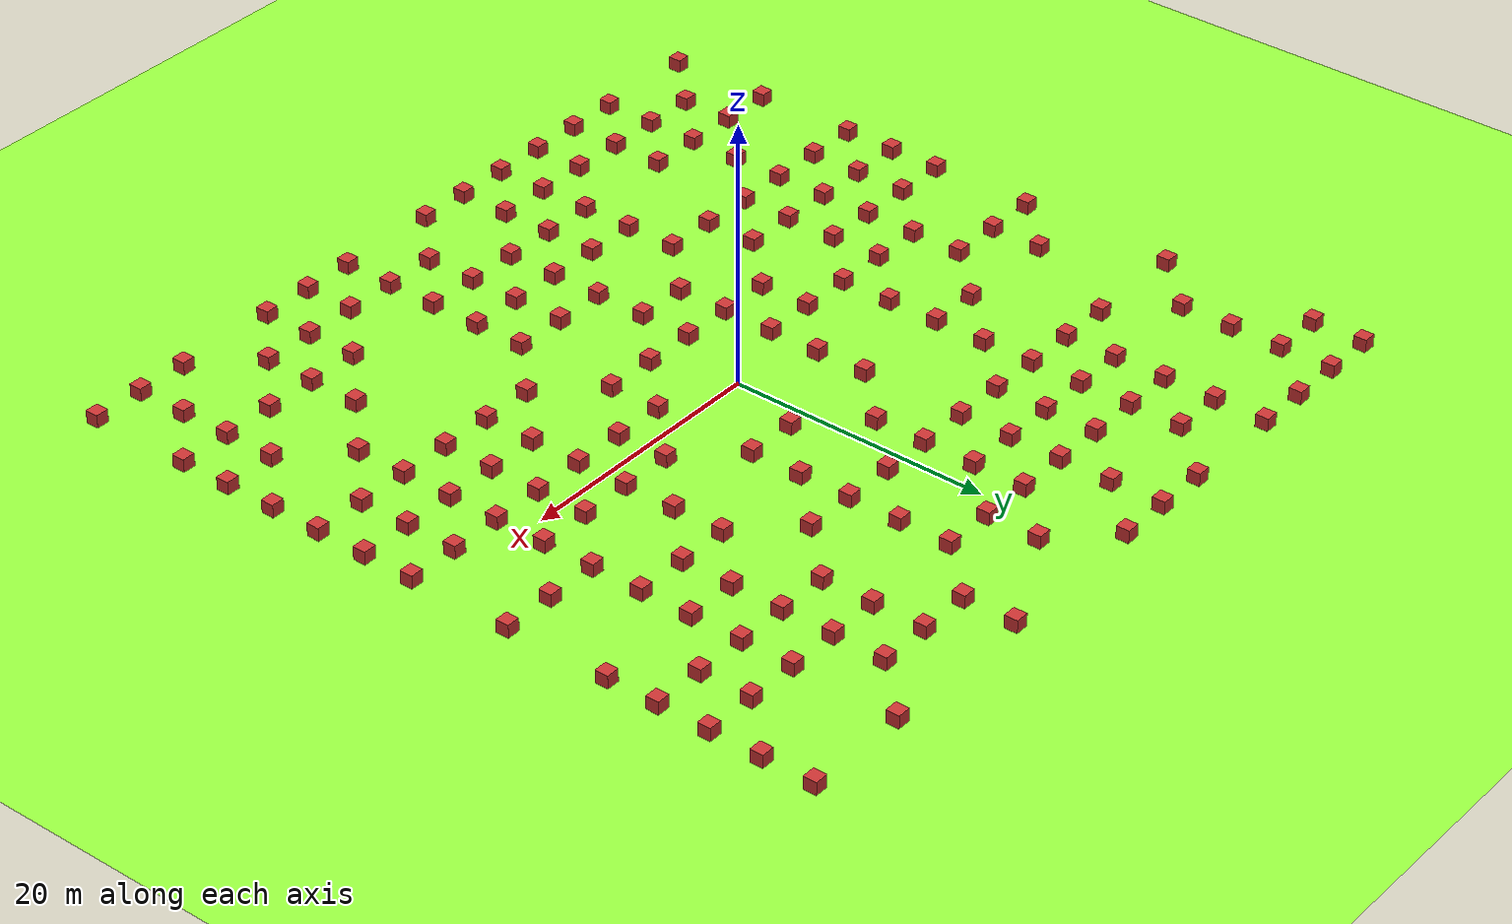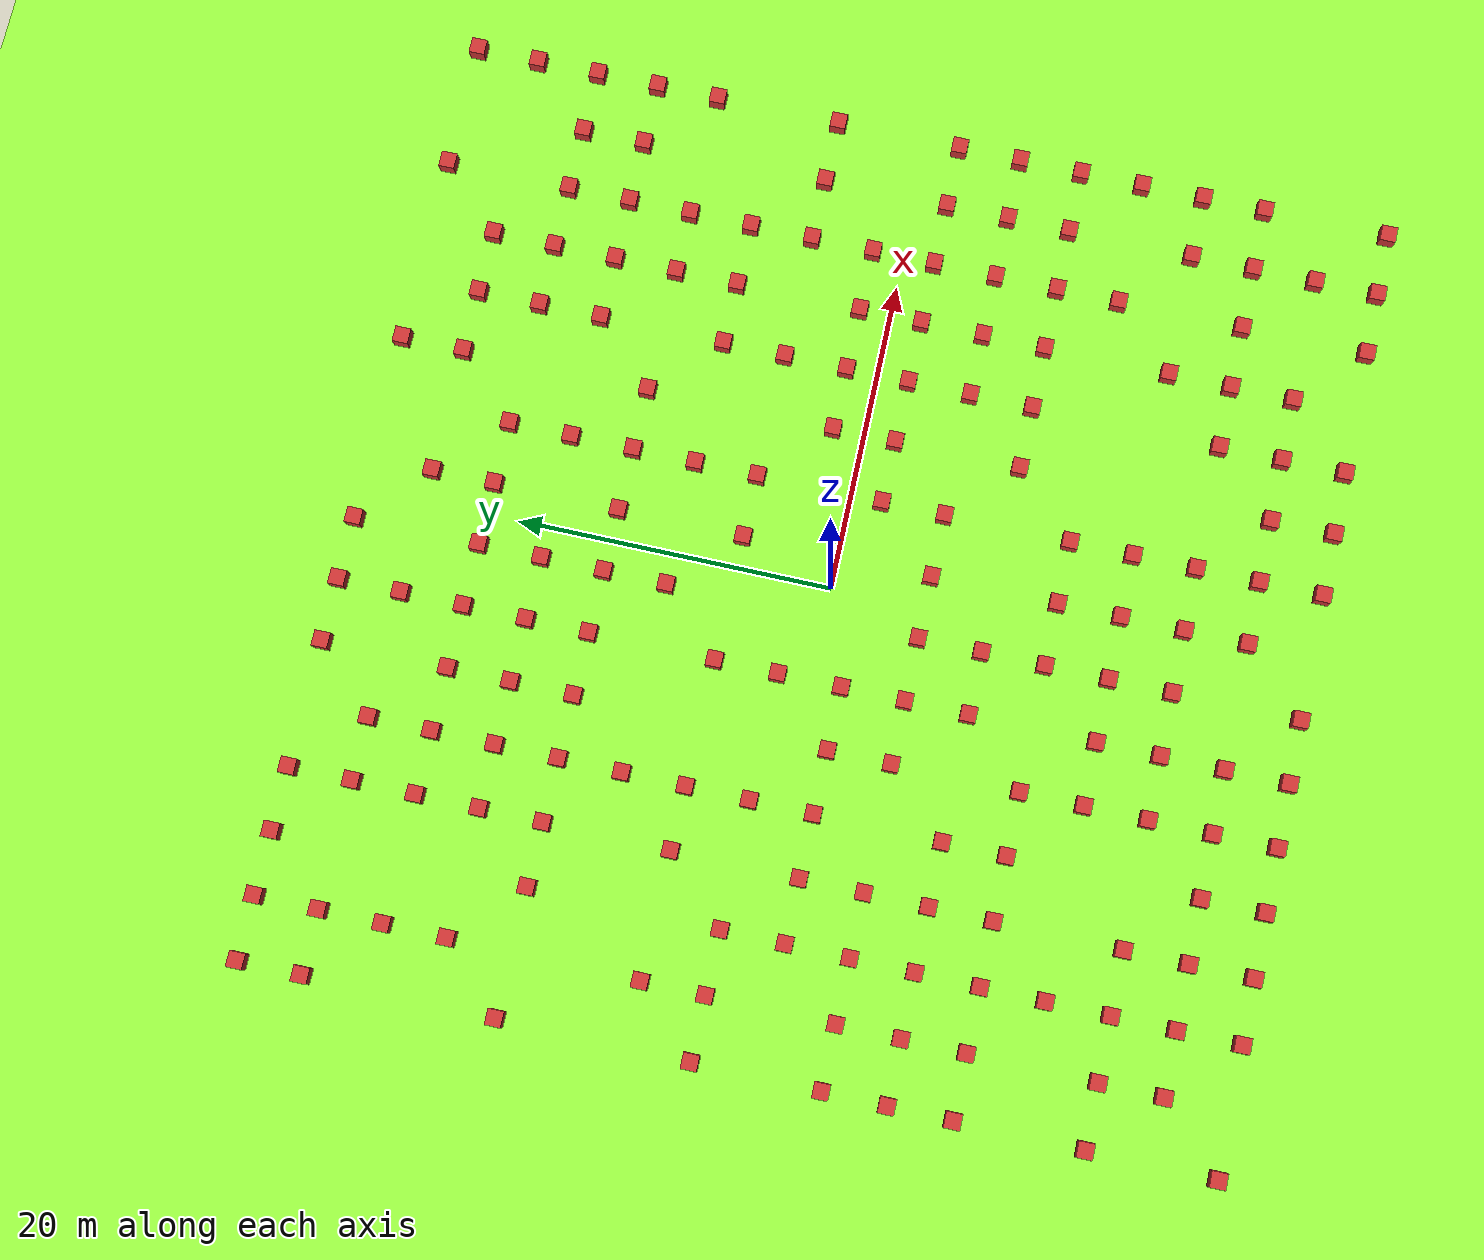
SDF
<?xml version="1.0" encoding="UTF-8"?>
<sdf version="1.9">
  <world name="lawn_boxes">
    <physics type="ode">
      <max_step_size>0.004</max_step_size>
      <real_time_factor>1.0</real_time_factor>
      <real_time_update_rate>250</real_time_update_rate>
    </physics>
    <gravity>0 0 -9.8</gravity>
    <magnetic_field>6e-06 2.3e-05 -4.2e-05</magnetic_field>
    <atmosphere type="adiabatic"/>
    <scene>
      <sky>
        <clouds>
          <speed>12</speed>
        </clouds>
      </sky>
      <grid>true</grid>
      <ambient>0.5 0.5 0.5 0.3</ambient>
      <background>0.3 0.3 0.3 0.3</background>
      <shadows>true</shadows>
    </scene>
    <model name="ground_plane">
      <static>true</static>
      <link name="link">
        <collision name="collision">
          <geometry>
            <plane>
              <normal>0 0 1</normal>
              <size>1 1</size>
            </plane>
          </geometry>
          <surface>
            <friction>
              <ode>
                <mu>0.6</mu>
                <mu2>0.6</mu2>
              </ode>
            </friction>
            <bounce/>
            <contact>
              <collide_bitmask>65535</collide_bitmask>
              <ode>
                <min_depth>0.005</min_depth>
                <kp>1e8</kp>
              </ode>
            </contact>
          </surface>
        </collision>
        <visual name="visual">
          <cast_shadows>false</cast_shadows>
          <geometry>
            <plane>
              <normal>0 0 1</normal>
              <size>400 400</size>
            </plane>
          </geometry>
          <material>
            <diffuse>0.6 1.0 0.25 0.5</diffuse>
            <specular>0 0 0 0</specular>
            <emissive>0 0 0 0</emissive>
          </material>
        </visual>
        <pose>0 0 0 0 -0 0</pose>
        <inertial>
          <pose>0 0 0 0 -0 0</pose>
          <mass>1</mass>
          <inertia>
            <ixx>1</ixx>
            <ixy>0</ixy>
            <ixz>0</ixz>
            <iyy>1</iyy>
            <iyz>0</iyz>
            <izz>1</izz>
          </inertia>
        </inertial>
        <enable_wind>false</enable_wind>
      </link>
      <pose>0 0 0 0 -0 0</pose>
      <self_collide>false</self_collide>
    </model>
    <light name="sunUTC" type="directional">
      <pose>0 0 500 0 -0 0</pose>
      <cast_shadows>true</cast_shadows>
      <intensity>1</intensity>
      <direction>0.001 0.625 -0.78</direction>
      <diffuse>0.904 0.904 0.904 1</diffuse>
      <specular>0.271 0.271 0.271 1</specular>
      <attenuation>
        <range>2000</range>
        <linear>0</linear>
        <constant>1</constant>
        <quadratic>0</quadratic>
      </attenuation>
      <spot>
        <inner_angle>0</inner_angle>
        <outer_angle>0</outer_angle>
        <falloff>0</falloff>
      </spot>
    </light>
    <light type="directional" name="sun_2">
      <cast_shadows>true</cast_shadows>
      <pose>200 200 200 0 0 0</pose>
      <diffuse>0.5 0.5 0.5 0.3</diffuse>
      <specular>0.2 0.2 0.2 0.3</specular>
      <attenuation>
        <range>2000</range>
        <constant>1</constant>
        <linear>0</linear>
        <quadratic>0</quadratic>
      </attenuation>
      <direction>0.01 0.01 -0.9</direction>
    </light>
    <spherical_coordinates>
      <surface_model>EARTH_WGS84</surface_model>
      <world_frame_orientation>ENU</world_frame_orientation>
      <latitude_deg>47.397971057728974</latitude_deg>
      <longitude_deg> 8.546163739800146</longitude_deg>
      <elevation>0</elevation>
    </spherical_coordinates>

    <model name="obstacle_box_0">
      <static>true</static>
      <pose>-30.00 -30.00 0.50 0 0 0</pose>
      <link name="link">
        <collision name="collision">
          <geometry>
            <box>
              <size>1.0 1.0 1.0</size>
            </box>
          </geometry>
        </collision>
        <visual name="visual">
          <geometry>
            <box>
              <size>1.0 1.0 1.0</size>
            </box>
          </geometry>
          <material>
            <diffuse>0.8 0.2 0.2 1</diffuse>
            <ambient>0.8 0.2 0.2 1</ambient>
          </material>
        </visual>
      </link>
    </model>

    <model name="obstacle_box_1">
      <static>true</static>
      <pose>-30.00 -22.00 0.50 0 0 0</pose>
      <link name="link">
        <collision name="collision">
          <geometry>
            <box>
              <size>1.0 1.0 1.0</size>
            </box>
          </geometry>
        </collision>
        <visual name="visual">
          <geometry>
            <box>
              <size>1.0 1.0 1.0</size>
            </box>
          </geometry>
          <material>
            <diffuse>0.8 0.2 0.2 1</diffuse>
            <ambient>0.8 0.2 0.2 1</ambient>
          </material>
        </visual>
      </link>
    </model>

    <model name="obstacle_box_2">
      <static>true</static>
      <pose>-30.00 -14.00 0.50 0 0 0</pose>
      <link name="link">
        <collision name="collision">
          <geometry>
            <box>
              <size>1.0 1.0 1.0</size>
            </box>
          </geometry>
        </collision>
        <visual name="visual">
          <geometry>
            <box>
              <size>1.0 1.0 1.0</size>
            </box>
          </geometry>
          <material>
            <diffuse>0.8 0.2 0.2 1</diffuse>
            <ambient>0.8 0.2 0.2 1</ambient>
          </material>
        </visual>
      </link>
    </model>

    <model name="obstacle_box_3">
      <static>true</static>
      <pose>-30.00 -10.00 0.50 0 0 0</pose>
      <link name="link">
        <collision name="collision">
          <geometry>
            <box>
              <size>1.0 1.0 1.0</size>
            </box>
          </geometry>
        </collision>
        <visual name="visual">
          <geometry>
            <box>
              <size>1.0 1.0 1.0</size>
            </box>
          </geometry>
          <material>
            <diffuse>0.8 0.2 0.2 1</diffuse>
            <ambient>0.8 0.2 0.2 1</ambient>
          </material>
        </visual>
      </link>
    </model>

    <model name="obstacle_box_4">
      <static>true</static>
      <pose>-30.00 -6.00 0.50 0 0 0</pose>
      <link name="link">
        <collision name="collision">
          <geometry>
            <box>
              <size>1.0 1.0 1.0</size>
            </box>
          </geometry>
        </collision>
        <visual name="visual">
          <geometry>
            <box>
              <size>1.0 1.0 1.0</size>
            </box>
          </geometry>
          <material>
            <diffuse>0.8 0.2 0.2 1</diffuse>
            <ambient>0.8 0.2 0.2 1</ambient>
          </material>
        </visual>
      </link>
    </model>

    <model name="obstacle_box_5">
      <static>true</static>
      <pose>-30.00 2.00 0.50 0 0 0</pose>
      <link name="link">
        <collision name="collision">
          <geometry>
            <box>
              <size>1.0 1.0 1.0</size>
            </box>
          </geometry>
        </collision>
        <visual name="visual">
          <geometry>
            <box>
              <size>1.0 1.0 1.0</size>
            </box>
          </geometry>
          <material>
            <diffuse>0.8 0.2 0.2 1</diffuse>
            <ambient>0.8 0.2 0.2 1</ambient>
          </material>
        </visual>
      </link>
    </model>

    <model name="obstacle_box_6">
      <static>true</static>
      <pose>-30.00 14.00 0.50 0 0 0</pose>
      <link name="link">
        <collision name="collision">
          <geometry>
            <box>
              <size>1.0 1.0 1.0</size>
            </box>
          </geometry>
        </collision>
        <visual name="visual">
          <geometry>
            <box>
              <size>1.0 1.0 1.0</size>
            </box>
          </geometry>
          <material>
            <diffuse>0.8 0.2 0.2 1</diffuse>
            <ambient>0.8 0.2 0.2 1</ambient>
          </material>
        </visual>
      </link>
    </model>

    <model name="obstacle_box_7">
      <static>true</static>
      <pose>-30.00 26.00 0.50 0 0 0</pose>
      <link name="link">
        <collision name="collision">
          <geometry>
            <box>
              <size>1.0 1.0 1.0</size>
            </box>
          </geometry>
        </collision>
        <visual name="visual">
          <geometry>
            <box>
              <size>1.0 1.0 1.0</size>
            </box>
          </geometry>
          <material>
            <diffuse>0.8 0.2 0.2 1</diffuse>
            <ambient>0.8 0.2 0.2 1</ambient>
          </material>
        </visual>
      </link>
    </model>

    <model name="obstacle_box_8">
      <static>true</static>
      <pose>-30.00 30.00 0.50 0 0 0</pose>
      <link name="link">
        <collision name="collision">
          <geometry>
            <box>
              <size>1.0 1.0 1.0</size>
            </box>
          </geometry>
        </collision>
        <visual name="visual">
          <geometry>
            <box>
              <size>1.0 1.0 1.0</size>
            </box>
          </geometry>
          <material>
            <diffuse>0.8 0.2 0.2 1</diffuse>
            <ambient>0.8 0.2 0.2 1</ambient>
          </material>
        </visual>
      </link>
    </model>

    <model name="obstacle_box_9">
      <static>true</static>
      <pose>-26.00 -26.00 0.50 0 0 0</pose>
      <link name="link">
        <collision name="collision">
          <geometry>
            <box>
              <size>1.0 1.0 1.0</size>
            </box>
          </geometry>
        </collision>
        <visual name="visual">
          <geometry>
            <box>
              <size>1.0 1.0 1.0</size>
            </box>
          </geometry>
          <material>
            <diffuse>0.8 0.2 0.2 1</diffuse>
            <ambient>0.8 0.2 0.2 1</ambient>
          </material>
        </visual>
      </link>
    </model>

    <model name="obstacle_box_10">
      <static>true</static>
      <pose>-26.00 -22.00 0.50 0 0 0</pose>
      <link name="link">
        <collision name="collision">
          <geometry>
            <box>
              <size>1.0 1.0 1.0</size>
            </box>
          </geometry>
        </collision>
        <visual name="visual">
          <geometry>
            <box>
              <size>1.0 1.0 1.0</size>
            </box>
          </geometry>
          <material>
            <diffuse>0.8 0.2 0.2 1</diffuse>
            <ambient>0.8 0.2 0.2 1</ambient>
          </material>
        </visual>
      </link>
    </model>

    <model name="obstacle_box_11">
      <static>true</static>
      <pose>-26.00 -14.00 0.50 0 0 0</pose>
      <link name="link">
        <collision name="collision">
          <geometry>
            <box>
              <size>1.0 1.0 1.0</size>
            </box>
          </geometry>
        </collision>
        <visual name="visual">
          <geometry>
            <box>
              <size>1.0 1.0 1.0</size>
            </box>
          </geometry>
          <material>
            <diffuse>0.8 0.2 0.2 1</diffuse>
            <ambient>0.8 0.2 0.2 1</ambient>
          </material>
        </visual>
      </link>
    </model>

    <model name="obstacle_box_12">
      <static>true</static>
      <pose>-26.00 -10.00 0.50 0 0 0</pose>
      <link name="link">
        <collision name="collision">
          <geometry>
            <box>
              <size>1.0 1.0 1.0</size>
            </box>
          </geometry>
        </collision>
        <visual name="visual">
          <geometry>
            <box>
              <size>1.0 1.0 1.0</size>
            </box>
          </geometry>
          <material>
            <diffuse>0.8 0.2 0.2 1</diffuse>
            <ambient>0.8 0.2 0.2 1</ambient>
          </material>
        </visual>
      </link>
    </model>

    <model name="obstacle_box_13">
      <static>true</static>
      <pose>-26.00 -6.00 0.50 0 0 0</pose>
      <link name="link">
        <collision name="collision">
          <geometry>
            <box>
              <size>1.0 1.0 1.0</size>
            </box>
          </geometry>
        </collision>
        <visual name="visual">
          <geometry>
            <box>
              <size>1.0 1.0 1.0</size>
            </box>
          </geometry>
          <material>
            <diffuse>0.8 0.2 0.2 1</diffuse>
            <ambient>0.8 0.2 0.2 1</ambient>
          </material>
        </visual>
      </link>
    </model>

    <model name="obstacle_box_14">
      <static>true</static>
      <pose>-26.00 2.00 0.50 0 0 0</pose>
      <link name="link">
        <collision name="collision">
          <geometry>
            <box>
              <size>1.0 1.0 1.0</size>
            </box>
          </geometry>
        </collision>
        <visual name="visual">
          <geometry>
            <box>
              <size>1.0 1.0 1.0</size>
            </box>
          </geometry>
          <material>
            <diffuse>0.8 0.2 0.2 1</diffuse>
            <ambient>0.8 0.2 0.2 1</ambient>
          </material>
        </visual>
      </link>
    </model>

    <model name="obstacle_box_15">
      <static>true</static>
      <pose>-26.00 6.00 0.50 0 0 0</pose>
      <link name="link">
        <collision name="collision">
          <geometry>
            <box>
              <size>1.0 1.0 1.0</size>
            </box>
          </geometry>
        </collision>
        <visual name="visual">
          <geometry>
            <box>
              <size>1.0 1.0 1.0</size>
            </box>
          </geometry>
          <material>
            <diffuse>0.8 0.2 0.2 1</diffuse>
            <ambient>0.8 0.2 0.2 1</ambient>
          </material>
        </visual>
      </link>
    </model>

    <model name="obstacle_box_16">
      <static>true</static>
      <pose>-26.00 18.00 0.50 0 0 0</pose>
      <link name="link">
        <collision name="collision">
          <geometry>
            <box>
              <size>1.0 1.0 1.0</size>
            </box>
          </geometry>
        </collision>
        <visual name="visual">
          <geometry>
            <box>
              <size>1.0 1.0 1.0</size>
            </box>
          </geometry>
          <material>
            <diffuse>0.8 0.2 0.2 1</diffuse>
            <ambient>0.8 0.2 0.2 1</ambient>
          </material>
        </visual>
      </link>
    </model>

    <model name="obstacle_box_17">
      <static>true</static>
      <pose>-26.00 22.00 0.50 0 0 0</pose>
      <link name="link">
        <collision name="collision">
          <geometry>
            <box>
              <size>1.0 1.0 1.0</size>
            </box>
          </geometry>
        </collision>
        <visual name="visual">
          <geometry>
            <box>
              <size>1.0 1.0 1.0</size>
            </box>
          </geometry>
          <material>
            <diffuse>0.8 0.2 0.2 1</diffuse>
            <ambient>0.8 0.2 0.2 1</ambient>
          </material>
        </visual>
      </link>
    </model>

    <model name="obstacle_box_18">
      <static>true</static>
      <pose>-26.00 26.00 0.50 0 0 0</pose>
      <link name="link">
        <collision name="collision">
          <geometry>
            <box>
              <size>1.0 1.0 1.0</size>
            </box>
          </geometry>
        </collision>
        <visual name="visual">
          <geometry>
            <box>
              <size>1.0 1.0 1.0</size>
            </box>
          </geometry>
          <material>
            <diffuse>0.8 0.2 0.2 1</diffuse>
            <ambient>0.8 0.2 0.2 1</ambient>
          </material>
        </visual>
      </link>
    </model>

    <model name="obstacle_box_19">
      <static>true</static>
      <pose>-26.00 30.00 0.50 0 0 0</pose>
      <link name="link">
        <collision name="collision">
          <geometry>
            <box>
              <size>1.0 1.0 1.0</size>
            </box>
          </geometry>
        </collision>
        <visual name="visual">
          <geometry>
            <box>
              <size>1.0 1.0 1.0</size>
            </box>
          </geometry>
          <material>
            <diffuse>0.8 0.2 0.2 1</diffuse>
            <ambient>0.8 0.2 0.2 1</ambient>
          </material>
        </visual>
      </link>
    </model>

    <model name="obstacle_box_20">
      <static>true</static>
      <pose>-22.00 -30.00 0.50 0 0 0</pose>
      <link name="link">
        <collision name="collision">
          <geometry>
            <box>
              <size>1.0 1.0 1.0</size>
            </box>
          </geometry>
        </collision>
        <visual name="visual">
          <geometry>
            <box>
              <size>1.0 1.0 1.0</size>
            </box>
          </geometry>
          <material>
            <diffuse>0.8 0.2 0.2 1</diffuse>
            <ambient>0.8 0.2 0.2 1</ambient>
          </material>
        </visual>
      </link>
    </model>

    <model name="obstacle_box_21">
      <static>true</static>
      <pose>-22.00 -26.00 0.50 0 0 0</pose>
      <link name="link">
        <collision name="collision">
          <geometry>
            <box>
              <size>1.0 1.0 1.0</size>
            </box>
          </geometry>
        </collision>
        <visual name="visual">
          <geometry>
            <box>
              <size>1.0 1.0 1.0</size>
            </box>
          </geometry>
          <material>
            <diffuse>0.8 0.2 0.2 1</diffuse>
            <ambient>0.8 0.2 0.2 1</ambient>
          </material>
        </visual>
      </link>
    </model>

    <model name="obstacle_box_22">
      <static>true</static>
      <pose>-22.00 -22.00 0.50 0 0 0</pose>
      <link name="link">
        <collision name="collision">
          <geometry>
            <box>
              <size>1.0 1.0 1.0</size>
            </box>
          </geometry>
        </collision>
        <visual name="visual">
          <geometry>
            <box>
              <size>1.0 1.0 1.0</size>
            </box>
          </geometry>
          <material>
            <diffuse>0.8 0.2 0.2 1</diffuse>
            <ambient>0.8 0.2 0.2 1</ambient>
          </material>
        </visual>
      </link>
    </model>

    <model name="obstacle_box_23">
      <static>true</static>
      <pose>-22.00 -18.00 0.50 0 0 0</pose>
      <link name="link">
        <collision name="collision">
          <geometry>
            <box>
              <size>1.0 1.0 1.0</size>
            </box>
          </geometry>
        </collision>
        <visual name="visual">
          <geometry>
            <box>
              <size>1.0 1.0 1.0</size>
            </box>
          </geometry>
          <material>
            <diffuse>0.8 0.2 0.2 1</diffuse>
            <ambient>0.8 0.2 0.2 1</ambient>
          </material>
        </visual>
      </link>
    </model>

    <model name="obstacle_box_24">
      <static>true</static>
      <pose>-22.00 -14.00 0.50 0 0 0</pose>
      <link name="link">
        <collision name="collision">
          <geometry>
            <box>
              <size>1.0 1.0 1.0</size>
            </box>
          </geometry>
        </collision>
        <visual name="visual">
          <geometry>
            <box>
              <size>1.0 1.0 1.0</size>
            </box>
          </geometry>
          <material>
            <diffuse>0.8 0.2 0.2 1</diffuse>
            <ambient>0.8 0.2 0.2 1</ambient>
          </material>
        </visual>
      </link>
    </model>

    <model name="obstacle_box_25">
      <static>true</static>
      <pose>-22.00 -10.00 0.50 0 0 0</pose>
      <link name="link">
        <collision name="collision">
          <geometry>
            <box>
              <size>1.0 1.0 1.0</size>
            </box>
          </geometry>
        </collision>
        <visual name="visual">
          <geometry>
            <box>
              <size>1.0 1.0 1.0</size>
            </box>
          </geometry>
          <material>
            <diffuse>0.8 0.2 0.2 1</diffuse>
            <ambient>0.8 0.2 0.2 1</ambient>
          </material>
        </visual>
      </link>
    </model>

    <model name="obstacle_box_26">
      <static>true</static>
      <pose>-22.00 -6.00 0.50 0 0 0</pose>
      <link name="link">
        <collision name="collision">
          <geometry>
            <box>
              <size>1.0 1.0 1.0</size>
            </box>
          </geometry>
        </collision>
        <visual name="visual">
          <geometry>
            <box>
              <size>1.0 1.0 1.0</size>
            </box>
          </geometry>
          <material>
            <diffuse>0.8 0.2 0.2 1</diffuse>
            <ambient>0.8 0.2 0.2 1</ambient>
          </material>
        </visual>
      </link>
    </model>

    <model name="obstacle_box_27">
      <static>true</static>
      <pose>-22.00 -2.00 0.50 0 0 0</pose>
      <link name="link">
        <collision name="collision">
          <geometry>
            <box>
              <size>1.0 1.0 1.0</size>
            </box>
          </geometry>
        </collision>
        <visual name="visual">
          <geometry>
            <box>
              <size>1.0 1.0 1.0</size>
            </box>
          </geometry>
          <material>
            <diffuse>0.8 0.2 0.2 1</diffuse>
            <ambient>0.8 0.2 0.2 1</ambient>
          </material>
        </visual>
      </link>
    </model>

    <model name="obstacle_box_28">
      <static>true</static>
      <pose>-22.00 2.00 0.50 0 0 0</pose>
      <link name="link">
        <collision name="collision">
          <geometry>
            <box>
              <size>1.0 1.0 1.0</size>
            </box>
          </geometry>
        </collision>
        <visual name="visual">
          <geometry>
            <box>
              <size>1.0 1.0 1.0</size>
            </box>
          </geometry>
          <material>
            <diffuse>0.8 0.2 0.2 1</diffuse>
            <ambient>0.8 0.2 0.2 1</ambient>
          </material>
        </visual>
      </link>
    </model>

    <model name="obstacle_box_29">
      <static>true</static>
      <pose>-22.00 14.00 0.50 0 0 0</pose>
      <link name="link">
        <collision name="collision">
          <geometry>
            <box>
              <size>1.0 1.0 1.0</size>
            </box>
          </geometry>
        </collision>
        <visual name="visual">
          <geometry>
            <box>
              <size>1.0 1.0 1.0</size>
            </box>
          </geometry>
          <material>
            <diffuse>0.8 0.2 0.2 1</diffuse>
            <ambient>0.8 0.2 0.2 1</ambient>
          </material>
        </visual>
      </link>
    </model>

    <model name="obstacle_box_30">
      <static>true</static>
      <pose>-22.00 30.00 0.50 0 0 0</pose>
      <link name="link">
        <collision name="collision">
          <geometry>
            <box>
              <size>1.0 1.0 1.0</size>
            </box>
          </geometry>
        </collision>
        <visual name="visual">
          <geometry>
            <box>
              <size>1.0 1.0 1.0</size>
            </box>
          </geometry>
          <material>
            <diffuse>0.8 0.2 0.2 1</diffuse>
            <ambient>0.8 0.2 0.2 1</ambient>
          </material>
        </visual>
      </link>
    </model>

    <model name="obstacle_box_31">
      <static>true</static>
      <pose>-18.00 -30.00 0.50 0 0 0</pose>
      <link name="link">
        <collision name="collision">
          <geometry>
            <box>
              <size>1.0 1.0 1.0</size>
            </box>
          </geometry>
        </collision>
        <visual name="visual">
          <geometry>
            <box>
              <size>1.0 1.0 1.0</size>
            </box>
          </geometry>
          <material>
            <diffuse>0.8 0.2 0.2 1</diffuse>
            <ambient>0.8 0.2 0.2 1</ambient>
          </material>
        </visual>
      </link>
    </model>

    <model name="obstacle_box_32">
      <static>true</static>
      <pose>-18.00 -26.00 0.50 0 0 0</pose>
      <link name="link">
        <collision name="collision">
          <geometry>
            <box>
              <size>1.0 1.0 1.0</size>
            </box>
          </geometry>
        </collision>
        <visual name="visual">
          <geometry>
            <box>
              <size>1.0 1.0 1.0</size>
            </box>
          </geometry>
          <material>
            <diffuse>0.8 0.2 0.2 1</diffuse>
            <ambient>0.8 0.2 0.2 1</ambient>
          </material>
        </visual>
      </link>
    </model>

    <model name="obstacle_box_33">
      <static>true</static>
      <pose>-18.00 -22.00 0.50 0 0 0</pose>
      <link name="link">
        <collision name="collision">
          <geometry>
            <box>
              <size>1.0 1.0 1.0</size>
            </box>
          </geometry>
        </collision>
        <visual name="visual">
          <geometry>
            <box>
              <size>1.0 1.0 1.0</size>
            </box>
          </geometry>
          <material>
            <diffuse>0.8 0.2 0.2 1</diffuse>
            <ambient>0.8 0.2 0.2 1</ambient>
          </material>
        </visual>
      </link>
    </model>

    <model name="obstacle_box_34">
      <static>true</static>
      <pose>-18.00 -14.00 0.50 0 0 0</pose>
      <link name="link">
        <collision name="collision">
          <geometry>
            <box>
              <size>1.0 1.0 1.0</size>
            </box>
          </geometry>
        </collision>
        <visual name="visual">
          <geometry>
            <box>
              <size>1.0 1.0 1.0</size>
            </box>
          </geometry>
          <material>
            <diffuse>0.8 0.2 0.2 1</diffuse>
            <ambient>0.8 0.2 0.2 1</ambient>
          </material>
        </visual>
      </link>
    </model>

    <model name="obstacle_box_35">
      <static>true</static>
      <pose>-18.00 -10.00 0.50 0 0 0</pose>
      <link name="link">
        <collision name="collision">
          <geometry>
            <box>
              <size>1.0 1.0 1.0</size>
            </box>
          </geometry>
        </collision>
        <visual name="visual">
          <geometry>
            <box>
              <size>1.0 1.0 1.0</size>
            </box>
          </geometry>
          <material>
            <diffuse>0.8 0.2 0.2 1</diffuse>
            <ambient>0.8 0.2 0.2 1</ambient>
          </material>
        </visual>
      </link>
    </model>

    <model name="obstacle_box_36">
      <static>true</static>
      <pose>-18.00 -6.00 0.50 0 0 0</pose>
      <link name="link">
        <collision name="collision">
          <geometry>
            <box>
              <size>1.0 1.0 1.0</size>
            </box>
          </geometry>
        </collision>
        <visual name="visual">
          <geometry>
            <box>
              <size>1.0 1.0 1.0</size>
            </box>
          </geometry>
          <material>
            <diffuse>0.8 0.2 0.2 1</diffuse>
            <ambient>0.8 0.2 0.2 1</ambient>
          </material>
        </visual>
      </link>
    </model>

    <model name="obstacle_box_37">
      <static>true</static>
      <pose>-18.00 -2.00 0.50 0 0 0</pose>
      <link name="link">
        <collision name="collision">
          <geometry>
            <box>
              <size>1.0 1.0 1.0</size>
            </box>
          </geometry>
        </collision>
        <visual name="visual">
          <geometry>
            <box>
              <size>1.0 1.0 1.0</size>
            </box>
          </geometry>
          <material>
            <diffuse>0.8 0.2 0.2 1</diffuse>
            <ambient>0.8 0.2 0.2 1</ambient>
          </material>
        </visual>
      </link>
    </model>

    <model name="obstacle_box_38">
      <static>true</static>
      <pose>-18.00 6.00 0.50 0 0 0</pose>
      <link name="link">
        <collision name="collision">
          <geometry>
            <box>
              <size>1.0 1.0 1.0</size>
            </box>
          </geometry>
        </collision>
        <visual name="visual">
          <geometry>
            <box>
              <size>1.0 1.0 1.0</size>
            </box>
          </geometry>
          <material>
            <diffuse>0.8 0.2 0.2 1</diffuse>
            <ambient>0.8 0.2 0.2 1</ambient>
          </material>
        </visual>
      </link>
    </model>

    <model name="obstacle_box_39">
      <static>true</static>
      <pose>-18.00 14.00 0.50 0 0 0</pose>
      <link name="link">
        <collision name="collision">
          <geometry>
            <box>
              <size>1.0 1.0 1.0</size>
            </box>
          </geometry>
        </collision>
        <visual name="visual">
          <geometry>
            <box>
              <size>1.0 1.0 1.0</size>
            </box>
          </geometry>
          <material>
            <diffuse>0.8 0.2 0.2 1</diffuse>
            <ambient>0.8 0.2 0.2 1</ambient>
          </material>
        </visual>
      </link>
    </model>

    <model name="obstacle_box_40">
      <static>true</static>
      <pose>-18.00 18.00 0.50 0 0 0</pose>
      <link name="link">
        <collision name="collision">
          <geometry>
            <box>
              <size>1.0 1.0 1.0</size>
            </box>
          </geometry>
        </collision>
        <visual name="visual">
          <geometry>
            <box>
              <size>1.0 1.0 1.0</size>
            </box>
          </geometry>
          <material>
            <diffuse>0.8 0.2 0.2 1</diffuse>
            <ambient>0.8 0.2 0.2 1</ambient>
          </material>
        </visual>
      </link>
    </model>

    <model name="obstacle_box_41">
      <static>true</static>
      <pose>-18.00 22.00 0.50 0 0 0</pose>
      <link name="link">
        <collision name="collision">
          <geometry>
            <box>
              <size>1.0 1.0 1.0</size>
            </box>
          </geometry>
        </collision>
        <visual name="visual">
          <geometry>
            <box>
              <size>1.0 1.0 1.0</size>
            </box>
          </geometry>
          <material>
            <diffuse>0.8 0.2 0.2 1</diffuse>
            <ambient>0.8 0.2 0.2 1</ambient>
          </material>
        </visual>
      </link>
    </model>

    <model name="obstacle_box_42">
      <static>true</static>
      <pose>-18.00 26.00 0.50 0 0 0</pose>
      <link name="link">
        <collision name="collision">
          <geometry>
            <box>
              <size>1.0 1.0 1.0</size>
            </box>
          </geometry>
        </collision>
        <visual name="visual">
          <geometry>
            <box>
              <size>1.0 1.0 1.0</size>
            </box>
          </geometry>
          <material>
            <diffuse>0.8 0.2 0.2 1</diffuse>
            <ambient>0.8 0.2 0.2 1</ambient>
          </material>
        </visual>
      </link>
    </model>

    <model name="obstacle_box_43">
      <static>true</static>
      <pose>-18.00 30.00 0.50 0 0 0</pose>
      <link name="link">
        <collision name="collision">
          <geometry>
            <box>
              <size>1.0 1.0 1.0</size>
            </box>
          </geometry>
        </collision>
        <visual name="visual">
          <geometry>
            <box>
              <size>1.0 1.0 1.0</size>
            </box>
          </geometry>
          <material>
            <diffuse>0.8 0.2 0.2 1</diffuse>
            <ambient>0.8 0.2 0.2 1</ambient>
          </material>
        </visual>
      </link>
    </model>

    <model name="obstacle_box_44">
      <static>true</static>
      <pose>-14.00 -30.00 0.50 0 0 0</pose>
      <link name="link">
        <collision name="collision">
          <geometry>
            <box>
              <size>1.0 1.0 1.0</size>
            </box>
          </geometry>
        </collision>
        <visual name="visual">
          <geometry>
            <box>
              <size>1.0 1.0 1.0</size>
            </box>
          </geometry>
          <material>
            <diffuse>0.8 0.2 0.2 1</diffuse>
            <ambient>0.8 0.2 0.2 1</ambient>
          </material>
        </visual>
      </link>
    </model>

    <model name="obstacle_box_45">
      <static>true</static>
      <pose>-14.00 -26.00 0.50 0 0 0</pose>
      <link name="link">
        <collision name="collision">
          <geometry>
            <box>
              <size>1.0 1.0 1.0</size>
            </box>
          </geometry>
        </collision>
        <visual name="visual">
          <geometry>
            <box>
              <size>1.0 1.0 1.0</size>
            </box>
          </geometry>
          <material>
            <diffuse>0.8 0.2 0.2 1</diffuse>
            <ambient>0.8 0.2 0.2 1</ambient>
          </material>
        </visual>
      </link>
    </model>

    <model name="obstacle_box_46">
      <static>true</static>
      <pose>-14.00 -14.00 0.50 0 0 0</pose>
      <link name="link">
        <collision name="collision">
          <geometry>
            <box>
              <size>1.0 1.0 1.0</size>
            </box>
          </geometry>
        </collision>
        <visual name="visual">
          <geometry>
            <box>
              <size>1.0 1.0 1.0</size>
            </box>
          </geometry>
          <material>
            <diffuse>0.8 0.2 0.2 1</diffuse>
            <ambient>0.8 0.2 0.2 1</ambient>
          </material>
        </visual>
      </link>
    </model>

    <model name="obstacle_box_47">
      <static>true</static>
      <pose>-14.00 -10.00 0.50 0 0 0</pose>
      <link name="link">
        <collision name="collision">
          <geometry>
            <box>
              <size>1.0 1.0 1.0</size>
            </box>
          </geometry>
        </collision>
        <visual name="visual">
          <geometry>
            <box>
              <size>1.0 1.0 1.0</size>
            </box>
          </geometry>
          <material>
            <diffuse>0.8 0.2 0.2 1</diffuse>
            <ambient>0.8 0.2 0.2 1</ambient>
          </material>
        </visual>
      </link>
    </model>

    <model name="obstacle_box_48">
      <static>true</static>
      <pose>-14.00 -2.00 0.50 0 0 0</pose>
      <link name="link">
        <collision name="collision">
          <geometry>
            <box>
              <size>1.0 1.0 1.0</size>
            </box>
          </geometry>
        </collision>
        <visual name="visual">
          <geometry>
            <box>
              <size>1.0 1.0 1.0</size>
            </box>
          </geometry>
          <material>
            <diffuse>0.8 0.2 0.2 1</diffuse>
            <ambient>0.8 0.2 0.2 1</ambient>
          </material>
        </visual>
      </link>
    </model>

    <model name="obstacle_box_49">
      <static>true</static>
      <pose>-14.00 2.00 0.50 0 0 0</pose>
      <link name="link">
        <collision name="collision">
          <geometry>
            <box>
              <size>1.0 1.0 1.0</size>
            </box>
          </geometry>
        </collision>
        <visual name="visual">
          <geometry>
            <box>
              <size>1.0 1.0 1.0</size>
            </box>
          </geometry>
          <material>
            <diffuse>0.8 0.2 0.2 1</diffuse>
            <ambient>0.8 0.2 0.2 1</ambient>
          </material>
        </visual>
      </link>
    </model>

    <model name="obstacle_box_50">
      <static>true</static>
      <pose>-14.00 6.00 0.50 0 0 0</pose>
      <link name="link">
        <collision name="collision">
          <geometry>
            <box>
              <size>1.0 1.0 1.0</size>
            </box>
          </geometry>
        </collision>
        <visual name="visual">
          <geometry>
            <box>
              <size>1.0 1.0 1.0</size>
            </box>
          </geometry>
          <material>
            <diffuse>0.8 0.2 0.2 1</diffuse>
            <ambient>0.8 0.2 0.2 1</ambient>
          </material>
        </visual>
      </link>
    </model>

    <model name="obstacle_box_51">
      <static>true</static>
      <pose>-14.00 10.00 0.50 0 0 0</pose>
      <link name="link">
        <collision name="collision">
          <geometry>
            <box>
              <size>1.0 1.0 1.0</size>
            </box>
          </geometry>
        </collision>
        <visual name="visual">
          <geometry>
            <box>
              <size>1.0 1.0 1.0</size>
            </box>
          </geometry>
          <material>
            <diffuse>0.8 0.2 0.2 1</diffuse>
            <ambient>0.8 0.2 0.2 1</ambient>
          </material>
        </visual>
      </link>
    </model>

    <model name="obstacle_box_52">
      <static>true</static>
      <pose>-14.00 14.00 0.50 0 0 0</pose>
      <link name="link">
        <collision name="collision">
          <geometry>
            <box>
              <size>1.0 1.0 1.0</size>
            </box>
          </geometry>
        </collision>
        <visual name="visual">
          <geometry>
            <box>
              <size>1.0 1.0 1.0</size>
            </box>
          </geometry>
          <material>
            <diffuse>0.8 0.2 0.2 1</diffuse>
            <ambient>0.8 0.2 0.2 1</ambient>
          </material>
        </visual>
      </link>
    </model>

    <model name="obstacle_box_53">
      <static>true</static>
      <pose>-14.00 18.00 0.50 0 0 0</pose>
      <link name="link">
        <collision name="collision">
          <geometry>
            <box>
              <size>1.0 1.0 1.0</size>
            </box>
          </geometry>
        </collision>
        <visual name="visual">
          <geometry>
            <box>
              <size>1.0 1.0 1.0</size>
            </box>
          </geometry>
          <material>
            <diffuse>0.8 0.2 0.2 1</diffuse>
            <ambient>0.8 0.2 0.2 1</ambient>
          </material>
        </visual>
      </link>
    </model>

    <model name="obstacle_box_54">
      <static>true</static>
      <pose>-14.00 22.00 0.50 0 0 0</pose>
      <link name="link">
        <collision name="collision">
          <geometry>
            <box>
              <size>1.0 1.0 1.0</size>
            </box>
          </geometry>
        </collision>
        <visual name="visual">
          <geometry>
            <box>
              <size>1.0 1.0 1.0</size>
            </box>
          </geometry>
          <material>
            <diffuse>0.8 0.2 0.2 1</diffuse>
            <ambient>0.8 0.2 0.2 1</ambient>
          </material>
        </visual>
      </link>
    </model>

    <model name="obstacle_box_55">
      <static>true</static>
      <pose>-14.00 26.00 0.50 0 0 0</pose>
      <link name="link">
        <collision name="collision">
          <geometry>
            <box>
              <size>1.0 1.0 1.0</size>
            </box>
          </geometry>
        </collision>
        <visual name="visual">
          <geometry>
            <box>
              <size>1.0 1.0 1.0</size>
            </box>
          </geometry>
          <material>
            <diffuse>0.8 0.2 0.2 1</diffuse>
            <ambient>0.8 0.2 0.2 1</ambient>
          </material>
        </visual>
      </link>
    </model>

    <model name="obstacle_box_56">
      <static>true</static>
      <pose>-10.00 -30.00 0.50 0 0 0</pose>
      <link name="link">
        <collision name="collision">
          <geometry>
            <box>
              <size>1.0 1.0 1.0</size>
            </box>
          </geometry>
        </collision>
        <visual name="visual">
          <geometry>
            <box>
              <size>1.0 1.0 1.0</size>
            </box>
          </geometry>
          <material>
            <diffuse>0.8 0.2 0.2 1</diffuse>
            <ambient>0.8 0.2 0.2 1</ambient>
          </material>
        </visual>
      </link>
    </model>

    <model name="obstacle_box_57">
      <static>true</static>
      <pose>-10.00 -26.00 0.50 0 0 0</pose>
      <link name="link">
        <collision name="collision">
          <geometry>
            <box>
              <size>1.0 1.0 1.0</size>
            </box>
          </geometry>
        </collision>
        <visual name="visual">
          <geometry>
            <box>
              <size>1.0 1.0 1.0</size>
            </box>
          </geometry>
          <material>
            <diffuse>0.8 0.2 0.2 1</diffuse>
            <ambient>0.8 0.2 0.2 1</ambient>
          </material>
        </visual>
      </link>
    </model>

    <model name="obstacle_box_58">
      <static>true</static>
      <pose>-10.00 -22.00 0.50 0 0 0</pose>
      <link name="link">
        <collision name="collision">
          <geometry>
            <box>
              <size>1.0 1.0 1.0</size>
            </box>
          </geometry>
        </collision>
        <visual name="visual">
          <geometry>
            <box>
              <size>1.0 1.0 1.0</size>
            </box>
          </geometry>
          <material>
            <diffuse>0.8 0.2 0.2 1</diffuse>
            <ambient>0.8 0.2 0.2 1</ambient>
          </material>
        </visual>
      </link>
    </model>

    <model name="obstacle_box_59">
      <static>true</static>
      <pose>-10.00 -18.00 0.50 0 0 0</pose>
      <link name="link">
        <collision name="collision">
          <geometry>
            <box>
              <size>1.0 1.0 1.0</size>
            </box>
          </geometry>
        </collision>
        <visual name="visual">
          <geometry>
            <box>
              <size>1.0 1.0 1.0</size>
            </box>
          </geometry>
          <material>
            <diffuse>0.8 0.2 0.2 1</diffuse>
            <ambient>0.8 0.2 0.2 1</ambient>
          </material>
        </visual>
      </link>
    </model>

    <model name="obstacle_box_60">
      <static>true</static>
      <pose>-10.00 -14.00 0.50 0 0 0</pose>
      <link name="link">
        <collision name="collision">
          <geometry>
            <box>
              <size>1.0 1.0 1.0</size>
            </box>
          </geometry>
        </collision>
        <visual name="visual">
          <geometry>
            <box>
              <size>1.0 1.0 1.0</size>
            </box>
          </geometry>
          <material>
            <diffuse>0.8 0.2 0.2 1</diffuse>
            <ambient>0.8 0.2 0.2 1</ambient>
          </material>
        </visual>
      </link>
    </model>

    <model name="obstacle_box_61">
      <static>true</static>
      <pose>-10.00 -6.00 0.50 0 0 0</pose>
      <link name="link">
        <collision name="collision">
          <geometry>
            <box>
              <size>1.0 1.0 1.0</size>
            </box>
          </geometry>
        </collision>
        <visual name="visual">
          <geometry>
            <box>
              <size>1.0 1.0 1.0</size>
            </box>
          </geometry>
          <material>
            <diffuse>0.8 0.2 0.2 1</diffuse>
            <ambient>0.8 0.2 0.2 1</ambient>
          </material>
        </visual>
      </link>
    </model>

    <model name="obstacle_box_62">
      <static>true</static>
      <pose>-10.00 -2.00 0.50 0 0 0</pose>
      <link name="link">
        <collision name="collision">
          <geometry>
            <box>
              <size>1.0 1.0 1.0</size>
            </box>
          </geometry>
        </collision>
        <visual name="visual">
          <geometry>
            <box>
              <size>1.0 1.0 1.0</size>
            </box>
          </geometry>
          <material>
            <diffuse>0.8 0.2 0.2 1</diffuse>
            <ambient>0.8 0.2 0.2 1</ambient>
          </material>
        </visual>
      </link>
    </model>

    <model name="obstacle_box_63">
      <static>true</static>
      <pose>-10.00 14.00 0.50 0 0 0</pose>
      <link name="link">
        <collision name="collision">
          <geometry>
            <box>
              <size>1.0 1.0 1.0</size>
            </box>
          </geometry>
        </collision>
        <visual name="visual">
          <geometry>
            <box>
              <size>1.0 1.0 1.0</size>
            </box>
          </geometry>
          <material>
            <diffuse>0.8 0.2 0.2 1</diffuse>
            <ambient>0.8 0.2 0.2 1</ambient>
          </material>
        </visual>
      </link>
    </model>

    <model name="obstacle_box_64">
      <static>true</static>
      <pose>-10.00 18.00 0.50 0 0 0</pose>
      <link name="link">
        <collision name="collision">
          <geometry>
            <box>
              <size>1.0 1.0 1.0</size>
            </box>
          </geometry>
        </collision>
        <visual name="visual">
          <geometry>
            <box>
              <size>1.0 1.0 1.0</size>
            </box>
          </geometry>
          <material>
            <diffuse>0.8 0.2 0.2 1</diffuse>
            <ambient>0.8 0.2 0.2 1</ambient>
          </material>
        </visual>
      </link>
    </model>

    <model name="obstacle_box_65">
      <static>true</static>
      <pose>-10.00 22.00 0.50 0 0 0</pose>
      <link name="link">
        <collision name="collision">
          <geometry>
            <box>
              <size>1.0 1.0 1.0</size>
            </box>
          </geometry>
        </collision>
        <visual name="visual">
          <geometry>
            <box>
              <size>1.0 1.0 1.0</size>
            </box>
          </geometry>
          <material>
            <diffuse>0.8 0.2 0.2 1</diffuse>
            <ambient>0.8 0.2 0.2 1</ambient>
          </material>
        </visual>
      </link>
    </model>

    <model name="obstacle_box_66">
      <static>true</static>
      <pose>-10.00 30.00 0.50 0 0 0</pose>
      <link name="link">
        <collision name="collision">
          <geometry>
            <box>
              <size>1.0 1.0 1.0</size>
            </box>
          </geometry>
        </collision>
        <visual name="visual">
          <geometry>
            <box>
              <size>1.0 1.0 1.0</size>
            </box>
          </geometry>
          <material>
            <diffuse>0.8 0.2 0.2 1</diffuse>
            <ambient>0.8 0.2 0.2 1</ambient>
          </material>
        </visual>
      </link>
    </model>

    <model name="obstacle_box_67">
      <static>true</static>
      <pose>-6.00 -30.00 0.50 0 0 0</pose>
      <link name="link">
        <collision name="collision">
          <geometry>
            <box>
              <size>1.0 1.0 1.0</size>
            </box>
          </geometry>
        </collision>
        <visual name="visual">
          <geometry>
            <box>
              <size>1.0 1.0 1.0</size>
            </box>
          </geometry>
          <material>
            <diffuse>0.8 0.2 0.2 1</diffuse>
            <ambient>0.8 0.2 0.2 1</ambient>
          </material>
        </visual>
      </link>
    </model>

    <model name="obstacle_box_68">
      <static>true</static>
      <pose>-6.00 -26.00 0.50 0 0 0</pose>
      <link name="link">
        <collision name="collision">
          <geometry>
            <box>
              <size>1.0 1.0 1.0</size>
            </box>
          </geometry>
        </collision>
        <visual name="visual">
          <geometry>
            <box>
              <size>1.0 1.0 1.0</size>
            </box>
          </geometry>
          <material>
            <diffuse>0.8 0.2 0.2 1</diffuse>
            <ambient>0.8 0.2 0.2 1</ambient>
          </material>
        </visual>
      </link>
    </model>

    <model name="obstacle_box_69">
      <static>true</static>
      <pose>-6.00 -22.00 0.50 0 0 0</pose>
      <link name="link">
        <collision name="collision">
          <geometry>
            <box>
              <size>1.0 1.0 1.0</size>
            </box>
          </geometry>
        </collision>
        <visual name="visual">
          <geometry>
            <box>
              <size>1.0 1.0 1.0</size>
            </box>
          </geometry>
          <material>
            <diffuse>0.8 0.2 0.2 1</diffuse>
            <ambient>0.8 0.2 0.2 1</ambient>
          </material>
        </visual>
      </link>
    </model>

    <model name="obstacle_box_70">
      <static>true</static>
      <pose>-6.00 -18.00 0.50 0 0 0</pose>
      <link name="link">
        <collision name="collision">
          <geometry>
            <box>
              <size>1.0 1.0 1.0</size>
            </box>
          </geometry>
        </collision>
        <visual name="visual">
          <geometry>
            <box>
              <size>1.0 1.0 1.0</size>
            </box>
          </geometry>
          <material>
            <diffuse>0.8 0.2 0.2 1</diffuse>
            <ambient>0.8 0.2 0.2 1</ambient>
          </material>
        </visual>
      </link>
    </model>

    <model name="obstacle_box_71">
      <static>true</static>
      <pose>-6.00 -10.00 0.50 0 0 0</pose>
      <link name="link">
        <collision name="collision">
          <geometry>
            <box>
              <size>1.0 1.0 1.0</size>
            </box>
          </geometry>
        </collision>
        <visual name="visual">
          <geometry>
            <box>
              <size>1.0 1.0 1.0</size>
            </box>
          </geometry>
          <material>
            <diffuse>0.8 0.2 0.2 1</diffuse>
            <ambient>0.8 0.2 0.2 1</ambient>
          </material>
        </visual>
      </link>
    </model>

    <model name="obstacle_box_72">
      <static>true</static>
      <pose>-6.00 -6.00 0.50 0 0 0</pose>
      <link name="link">
        <collision name="collision">
          <geometry>
            <box>
              <size>1.0 1.0 1.0</size>
            </box>
          </geometry>
        </collision>
        <visual name="visual">
          <geometry>
            <box>
              <size>1.0 1.0 1.0</size>
            </box>
          </geometry>
          <material>
            <diffuse>0.8 0.2 0.2 1</diffuse>
            <ambient>0.8 0.2 0.2 1</ambient>
          </material>
        </visual>
      </link>
    </model>

    <model name="obstacle_box_73">
      <static>true</static>
      <pose>-6.00 -2.00 0.50 0 0 0</pose>
      <link name="link">
        <collision name="collision">
          <geometry>
            <box>
              <size>1.0 1.0 1.0</size>
            </box>
          </geometry>
        </collision>
        <visual name="visual">
          <geometry>
            <box>
              <size>1.0 1.0 1.0</size>
            </box>
          </geometry>
          <material>
            <diffuse>0.8 0.2 0.2 1</diffuse>
            <ambient>0.8 0.2 0.2 1</ambient>
          </material>
        </visual>
      </link>
    </model>

    <model name="obstacle_box_74">
      <static>true</static>
      <pose>-6.00 2.00 0.50 0 0 0</pose>
      <link name="link">
        <collision name="collision">
          <geometry>
            <box>
              <size>1.0 1.0 1.0</size>
            </box>
          </geometry>
        </collision>
        <visual name="visual">
          <geometry>
            <box>
              <size>1.0 1.0 1.0</size>
            </box>
          </geometry>
          <material>
            <diffuse>0.8 0.2 0.2 1</diffuse>
            <ambient>0.8 0.2 0.2 1</ambient>
          </material>
        </visual>
      </link>
    </model>

    <model name="obstacle_box_75">
      <static>true</static>
      <pose>-6.00 6.00 0.50 0 0 0</pose>
      <link name="link">
        <collision name="collision">
          <geometry>
            <box>
              <size>1.0 1.0 1.0</size>
            </box>
          </geometry>
        </collision>
        <visual name="visual">
          <geometry>
            <box>
              <size>1.0 1.0 1.0</size>
            </box>
          </geometry>
          <material>
            <diffuse>0.8 0.2 0.2 1</diffuse>
            <ambient>0.8 0.2 0.2 1</ambient>
          </material>
        </visual>
      </link>
    </model>

    <model name="obstacle_box_76">
      <static>true</static>
      <pose>-6.00 14.00 0.50 0 0 0</pose>
      <link name="link">
        <collision name="collision">
          <geometry>
            <box>
              <size>1.0 1.0 1.0</size>
            </box>
          </geometry>
        </collision>
        <visual name="visual">
          <geometry>
            <box>
              <size>1.0 1.0 1.0</size>
            </box>
          </geometry>
          <material>
            <diffuse>0.8 0.2 0.2 1</diffuse>
            <ambient>0.8 0.2 0.2 1</ambient>
          </material>
        </visual>
      </link>
    </model>

    <model name="obstacle_box_77">
      <static>true</static>
      <pose>-6.00 18.00 0.50 0 0 0</pose>
      <link name="link">
        <collision name="collision">
          <geometry>
            <box>
              <size>1.0 1.0 1.0</size>
            </box>
          </geometry>
        </collision>
        <visual name="visual">
          <geometry>
            <box>
              <size>1.0 1.0 1.0</size>
            </box>
          </geometry>
          <material>
            <diffuse>0.8 0.2 0.2 1</diffuse>
            <ambient>0.8 0.2 0.2 1</ambient>
          </material>
        </visual>
      </link>
    </model>

    <model name="obstacle_box_78">
      <static>true</static>
      <pose>-6.00 22.00 0.50 0 0 0</pose>
      <link name="link">
        <collision name="collision">
          <geometry>
            <box>
              <size>1.0 1.0 1.0</size>
            </box>
          </geometry>
        </collision>
        <visual name="visual">
          <geometry>
            <box>
              <size>1.0 1.0 1.0</size>
            </box>
          </geometry>
          <material>
            <diffuse>0.8 0.2 0.2 1</diffuse>
            <ambient>0.8 0.2 0.2 1</ambient>
          </material>
        </visual>
      </link>
    </model>

    <model name="obstacle_box_79">
      <static>true</static>
      <pose>-6.00 26.00 0.50 0 0 0</pose>
      <link name="link">
        <collision name="collision">
          <geometry>
            <box>
              <size>1.0 1.0 1.0</size>
            </box>
          </geometry>
        </collision>
        <visual name="visual">
          <geometry>
            <box>
              <size>1.0 1.0 1.0</size>
            </box>
          </geometry>
          <material>
            <diffuse>0.8 0.2 0.2 1</diffuse>
            <ambient>0.8 0.2 0.2 1</ambient>
          </material>
        </visual>
      </link>
    </model>

    <model name="obstacle_box_80">
      <static>true</static>
      <pose>-6.00 30.00 0.50 0 0 0</pose>
      <link name="link">
        <collision name="collision">
          <geometry>
            <box>
              <size>1.0 1.0 1.0</size>
            </box>
          </geometry>
        </collision>
        <visual name="visual">
          <geometry>
            <box>
              <size>1.0 1.0 1.0</size>
            </box>
          </geometry>
          <material>
            <diffuse>0.8 0.2 0.2 1</diffuse>
            <ambient>0.8 0.2 0.2 1</ambient>
          </material>
        </visual>
      </link>
    </model>

    <model name="obstacle_box_81">
      <static>true</static>
      <pose>-2.00 -30.00 0.50 0 0 0</pose>
      <link name="link">
        <collision name="collision">
          <geometry>
            <box>
              <size>1.0 1.0 1.0</size>
            </box>
          </geometry>
        </collision>
        <visual name="visual">
          <geometry>
            <box>
              <size>1.0 1.0 1.0</size>
            </box>
          </geometry>
          <material>
            <diffuse>0.8 0.2 0.2 1</diffuse>
            <ambient>0.8 0.2 0.2 1</ambient>
          </material>
        </visual>
      </link>
    </model>

    <model name="obstacle_box_82">
      <static>true</static>
      <pose>-2.00 -22.00 0.50 0 0 0</pose>
      <link name="link">
        <collision name="collision">
          <geometry>
            <box>
              <size>1.0 1.0 1.0</size>
            </box>
          </geometry>
        </collision>
        <visual name="visual">
          <geometry>
            <box>
              <size>1.0 1.0 1.0</size>
            </box>
          </geometry>
          <material>
            <diffuse>0.8 0.2 0.2 1</diffuse>
            <ambient>0.8 0.2 0.2 1</ambient>
          </material>
        </visual>
      </link>
    </model>

    <model name="obstacle_box_83">
      <static>true</static>
      <pose>-2.00 -18.00 0.50 0 0 0</pose>
      <link name="link">
        <collision name="collision">
          <geometry>
            <box>
              <size>1.0 1.0 1.0</size>
            </box>
          </geometry>
        </collision>
        <visual name="visual">
          <geometry>
            <box>
              <size>1.0 1.0 1.0</size>
            </box>
          </geometry>
          <material>
            <diffuse>0.8 0.2 0.2 1</diffuse>
            <ambient>0.8 0.2 0.2 1</ambient>
          </material>
        </visual>
      </link>
    </model>

    <model name="obstacle_box_84">
      <static>true</static>
      <pose>-2.00 -14.00 0.50 0 0 0</pose>
      <link name="link">
        <collision name="collision">
          <geometry>
            <box>
              <size>1.0 1.0 1.0</size>
            </box>
          </geometry>
        </collision>
        <visual name="visual">
          <geometry>
            <box>
              <size>1.0 1.0 1.0</size>
            </box>
          </geometry>
          <material>
            <diffuse>0.8 0.2 0.2 1</diffuse>
            <ambient>0.8 0.2 0.2 1</ambient>
          </material>
        </visual>
      </link>
    </model>

    <model name="obstacle_box_85">
      <static>true</static>
      <pose>-2.00 -10.00 0.50 0 0 0</pose>
      <link name="link">
        <collision name="collision">
          <geometry>
            <box>
              <size>1.0 1.0 1.0</size>
            </box>
          </geometry>
        </collision>
        <visual name="visual">
          <geometry>
            <box>
              <size>1.0 1.0 1.0</size>
            </box>
          </geometry>
          <material>
            <diffuse>0.8 0.2 0.2 1</diffuse>
            <ambient>0.8 0.2 0.2 1</ambient>
          </material>
        </visual>
      </link>
    </model>

    <model name="obstacle_box_86">
      <static>true</static>
      <pose>-2.00 -6.00 0.50 0 0 0</pose>
      <link name="link">
        <collision name="collision">
          <geometry>
            <box>
              <size>1.0 1.0 1.0</size>
            </box>
          </geometry>
        </collision>
        <visual name="visual">
          <geometry>
            <box>
              <size>1.0 1.0 1.0</size>
            </box>
          </geometry>
          <material>
            <diffuse>0.8 0.2 0.2 1</diffuse>
            <ambient>0.8 0.2 0.2 1</ambient>
          </material>
        </visual>
      </link>
    </model>

    <model name="obstacle_box_87">
      <static>true</static>
      <pose>-2.00 10.00 0.50 0 0 0</pose>
      <link name="link">
        <collision name="collision">
          <geometry>
            <box>
              <size>1.0 1.0 1.0</size>
            </box>
          </geometry>
        </collision>
        <visual name="visual">
          <geometry>
            <box>
              <size>1.0 1.0 1.0</size>
            </box>
          </geometry>
          <material>
            <diffuse>0.8 0.2 0.2 1</diffuse>
            <ambient>0.8 0.2 0.2 1</ambient>
          </material>
        </visual>
      </link>
    </model>

    <model name="obstacle_box_88">
      <static>true</static>
      <pose>-2.00 14.00 0.50 0 0 0</pose>
      <link name="link">
        <collision name="collision">
          <geometry>
            <box>
              <size>1.0 1.0 1.0</size>
            </box>
          </geometry>
        </collision>
        <visual name="visual">
          <geometry>
            <box>
              <size>1.0 1.0 1.0</size>
            </box>
          </geometry>
          <material>
            <diffuse>0.8 0.2 0.2 1</diffuse>
            <ambient>0.8 0.2 0.2 1</ambient>
          </material>
        </visual>
      </link>
    </model>

    <model name="obstacle_box_89">
      <static>true</static>
      <pose>-2.00 18.00 0.50 0 0 0</pose>
      <link name="link">
        <collision name="collision">
          <geometry>
            <box>
              <size>1.0 1.0 1.0</size>
            </box>
          </geometry>
        </collision>
        <visual name="visual">
          <geometry>
            <box>
              <size>1.0 1.0 1.0</size>
            </box>
          </geometry>
          <material>
            <diffuse>0.8 0.2 0.2 1</diffuse>
            <ambient>0.8 0.2 0.2 1</ambient>
          </material>
        </visual>
      </link>
    </model>

    <model name="obstacle_box_90">
      <static>true</static>
      <pose>-2.00 22.00 0.50 0 0 0</pose>
      <link name="link">
        <collision name="collision">
          <geometry>
            <box>
              <size>1.0 1.0 1.0</size>
            </box>
          </geometry>
        </collision>
        <visual name="visual">
          <geometry>
            <box>
              <size>1.0 1.0 1.0</size>
            </box>
          </geometry>
          <material>
            <diffuse>0.8 0.2 0.2 1</diffuse>
            <ambient>0.8 0.2 0.2 1</ambient>
          </material>
        </visual>
      </link>
    </model>

    <model name="obstacle_box_91">
      <static>true</static>
      <pose>-2.00 30.00 0.50 0 0 0</pose>
      <link name="link">
        <collision name="collision">
          <geometry>
            <box>
              <size>1.0 1.0 1.0</size>
            </box>
          </geometry>
        </collision>
        <visual name="visual">
          <geometry>
            <box>
              <size>1.0 1.0 1.0</size>
            </box>
          </geometry>
          <material>
            <diffuse>0.8 0.2 0.2 1</diffuse>
            <ambient>0.8 0.2 0.2 1</ambient>
          </material>
        </visual>
      </link>
    </model>

    <model name="obstacle_box_92">
      <static>true</static>
      <pose>2.00 -26.00 0.50 0 0 0</pose>
      <link name="link">
        <collision name="collision">
          <geometry>
            <box>
              <size>1.0 1.0 1.0</size>
            </box>
          </geometry>
        </collision>
        <visual name="visual">
          <geometry>
            <box>
              <size>1.0 1.0 1.0</size>
            </box>
          </geometry>
          <material>
            <diffuse>0.8 0.2 0.2 1</diffuse>
            <ambient>0.8 0.2 0.2 1</ambient>
          </material>
        </visual>
      </link>
    </model>

    <model name="obstacle_box_93">
      <static>true</static>
      <pose>2.00 -22.00 0.50 0 0 0</pose>
      <link name="link">
        <collision name="collision">
          <geometry>
            <box>
              <size>1.0 1.0 1.0</size>
            </box>
          </geometry>
        </collision>
        <visual name="visual">
          <geometry>
            <box>
              <size>1.0 1.0 1.0</size>
            </box>
          </geometry>
          <material>
            <diffuse>0.8 0.2 0.2 1</diffuse>
            <ambient>0.8 0.2 0.2 1</ambient>
          </material>
        </visual>
      </link>
    </model>

    <model name="obstacle_box_94">
      <static>true</static>
      <pose>2.00 -18.00 0.50 0 0 0</pose>
      <link name="link">
        <collision name="collision">
          <geometry>
            <box>
              <size>1.0 1.0 1.0</size>
            </box>
          </geometry>
        </collision>
        <visual name="visual">
          <geometry>
            <box>
              <size>1.0 1.0 1.0</size>
            </box>
          </geometry>
          <material>
            <diffuse>0.8 0.2 0.2 1</diffuse>
            <ambient>0.8 0.2 0.2 1</ambient>
          </material>
        </visual>
      </link>
    </model>

    <model name="obstacle_box_95">
      <static>true</static>
      <pose>2.00 -14.00 0.50 0 0 0</pose>
      <link name="link">
        <collision name="collision">
          <geometry>
            <box>
              <size>1.0 1.0 1.0</size>
            </box>
          </geometry>
        </collision>
        <visual name="visual">
          <geometry>
            <box>
              <size>1.0 1.0 1.0</size>
            </box>
          </geometry>
          <material>
            <diffuse>0.8 0.2 0.2 1</diffuse>
            <ambient>0.8 0.2 0.2 1</ambient>
          </material>
        </visual>
      </link>
    </model>

    <model name="obstacle_box_96">
      <static>true</static>
      <pose>2.00 -6.00 0.50 0 0 0</pose>
      <link name="link">
        <collision name="collision">
          <geometry>
            <box>
              <size>1.0 1.0 1.0</size>
            </box>
          </geometry>
        </collision>
        <visual name="visual">
          <geometry>
            <box>
              <size>1.0 1.0 1.0</size>
            </box>
          </geometry>
          <material>
            <diffuse>0.8 0.2 0.2 1</diffuse>
            <ambient>0.8 0.2 0.2 1</ambient>
          </material>
        </visual>
      </link>
    </model>

    <model name="obstacle_box_97">
      <static>true</static>
      <pose>2.00 6.00 0.50 0 0 0</pose>
      <link name="link">
        <collision name="collision">
          <geometry>
            <box>
              <size>1.0 1.0 1.0</size>
            </box>
          </geometry>
        </collision>
        <visual name="visual">
          <geometry>
            <box>
              <size>1.0 1.0 1.0</size>
            </box>
          </geometry>
          <material>
            <diffuse>0.8 0.2 0.2 1</diffuse>
            <ambient>0.8 0.2 0.2 1</ambient>
          </material>
        </visual>
      </link>
    </model>

    <model name="obstacle_box_98">
      <static>true</static>
      <pose>2.00 14.00 0.50 0 0 0</pose>
      <link name="link">
        <collision name="collision">
          <geometry>
            <box>
              <size>1.0 1.0 1.0</size>
            </box>
          </geometry>
        </collision>
        <visual name="visual">
          <geometry>
            <box>
              <size>1.0 1.0 1.0</size>
            </box>
          </geometry>
          <material>
            <diffuse>0.8 0.2 0.2 1</diffuse>
            <ambient>0.8 0.2 0.2 1</ambient>
          </material>
        </visual>
      </link>
    </model>

    <model name="obstacle_box_99">
      <static>true</static>
      <pose>2.00 22.00 0.50 0 0 0</pose>
      <link name="link">
        <collision name="collision">
          <geometry>
            <box>
              <size>1.0 1.0 1.0</size>
            </box>
          </geometry>
        </collision>
        <visual name="visual">
          <geometry>
            <box>
              <size>1.0 1.0 1.0</size>
            </box>
          </geometry>
          <material>
            <diffuse>0.8 0.2 0.2 1</diffuse>
            <ambient>0.8 0.2 0.2 1</ambient>
          </material>
        </visual>
      </link>
    </model>

    <model name="obstacle_box_100">
      <static>true</static>
      <pose>2.00 26.00 0.50 0 0 0</pose>
      <link name="link">
        <collision name="collision">
          <geometry>
            <box>
              <size>1.0 1.0 1.0</size>
            </box>
          </geometry>
        </collision>
        <visual name="visual">
          <geometry>
            <box>
              <size>1.0 1.0 1.0</size>
            </box>
          </geometry>
          <material>
            <diffuse>0.8 0.2 0.2 1</diffuse>
            <ambient>0.8 0.2 0.2 1</ambient>
          </material>
        </visual>
      </link>
    </model>

    <model name="obstacle_box_101">
      <static>true</static>
      <pose>6.00 -30.00 0.50 0 0 0</pose>
      <link name="link">
        <collision name="collision">
          <geometry>
            <box>
              <size>1.0 1.0 1.0</size>
            </box>
          </geometry>
        </collision>
        <visual name="visual">
          <geometry>
            <box>
              <size>1.0 1.0 1.0</size>
            </box>
          </geometry>
          <material>
            <diffuse>0.8 0.2 0.2 1</diffuse>
            <ambient>0.8 0.2 0.2 1</ambient>
          </material>
        </visual>
      </link>
    </model>

    <model name="obstacle_box_102">
      <static>true</static>
      <pose>6.00 -26.00 0.50 0 0 0</pose>
      <link name="link">
        <collision name="collision">
          <geometry>
            <box>
              <size>1.0 1.0 1.0</size>
            </box>
          </geometry>
        </collision>
        <visual name="visual">
          <geometry>
            <box>
              <size>1.0 1.0 1.0</size>
            </box>
          </geometry>
          <material>
            <diffuse>0.8 0.2 0.2 1</diffuse>
            <ambient>0.8 0.2 0.2 1</ambient>
          </material>
        </visual>
      </link>
    </model>

    <model name="obstacle_box_103">
      <static>true</static>
      <pose>6.00 -22.00 0.50 0 0 0</pose>
      <link name="link">
        <collision name="collision">
          <geometry>
            <box>
              <size>1.0 1.0 1.0</size>
            </box>
          </geometry>
        </collision>
        <visual name="visual">
          <geometry>
            <box>
              <size>1.0 1.0 1.0</size>
            </box>
          </geometry>
          <material>
            <diffuse>0.8 0.2 0.2 1</diffuse>
            <ambient>0.8 0.2 0.2 1</ambient>
          </material>
        </visual>
      </link>
    </model>

    <model name="obstacle_box_104">
      <static>true</static>
      <pose>6.00 -18.00 0.50 0 0 0</pose>
      <link name="link">
        <collision name="collision">
          <geometry>
            <box>
              <size>1.0 1.0 1.0</size>
            </box>
          </geometry>
        </collision>
        <visual name="visual">
          <geometry>
            <box>
              <size>1.0 1.0 1.0</size>
            </box>
          </geometry>
          <material>
            <diffuse>0.8 0.2 0.2 1</diffuse>
            <ambient>0.8 0.2 0.2 1</ambient>
          </material>
        </visual>
      </link>
    </model>

    <model name="obstacle_box_105">
      <static>true</static>
      <pose>6.00 -14.00 0.50 0 0 0</pose>
      <link name="link">
        <collision name="collision">
          <geometry>
            <box>
              <size>1.0 1.0 1.0</size>
            </box>
          </geometry>
        </collision>
        <visual name="visual">
          <geometry>
            <box>
              <size>1.0 1.0 1.0</size>
            </box>
          </geometry>
          <material>
            <diffuse>0.8 0.2 0.2 1</diffuse>
            <ambient>0.8 0.2 0.2 1</ambient>
          </material>
        </visual>
      </link>
    </model>

    <model name="obstacle_box_106">
      <static>true</static>
      <pose>6.00 -6.00 0.50 0 0 0</pose>
      <link name="link">
        <collision name="collision">
          <geometry>
            <box>
              <size>1.0 1.0 1.0</size>
            </box>
          </geometry>
        </collision>
        <visual name="visual">
          <geometry>
            <box>
              <size>1.0 1.0 1.0</size>
            </box>
          </geometry>
          <material>
            <diffuse>0.8 0.2 0.2 1</diffuse>
            <ambient>0.8 0.2 0.2 1</ambient>
          </material>
        </visual>
      </link>
    </model>

    <model name="obstacle_box_107">
      <static>true</static>
      <pose>6.00 -2.00 0.50 0 0 0</pose>
      <link name="link">
        <collision name="collision">
          <geometry>
            <box>
              <size>1.0 1.0 1.0</size>
            </box>
          </geometry>
        </collision>
        <visual name="visual">
          <geometry>
            <box>
              <size>1.0 1.0 1.0</size>
            </box>
          </geometry>
          <material>
            <diffuse>0.8 0.2 0.2 1</diffuse>
            <ambient>0.8 0.2 0.2 1</ambient>
          </material>
        </visual>
      </link>
    </model>

    <model name="obstacle_box_108">
      <static>true</static>
      <pose>6.00 6.00 0.50 0 0 0</pose>
      <link name="link">
        <collision name="collision">
          <geometry>
            <box>
              <size>1.0 1.0 1.0</size>
            </box>
          </geometry>
        </collision>
        <visual name="visual">
          <geometry>
            <box>
              <size>1.0 1.0 1.0</size>
            </box>
          </geometry>
          <material>
            <diffuse>0.8 0.2 0.2 1</diffuse>
            <ambient>0.8 0.2 0.2 1</ambient>
          </material>
        </visual>
      </link>
    </model>

    <model name="obstacle_box_109">
      <static>true</static>
      <pose>6.00 10.00 0.50 0 0 0</pose>
      <link name="link">
        <collision name="collision">
          <geometry>
            <box>
              <size>1.0 1.0 1.0</size>
            </box>
          </geometry>
        </collision>
        <visual name="visual">
          <geometry>
            <box>
              <size>1.0 1.0 1.0</size>
            </box>
          </geometry>
          <material>
            <diffuse>0.8 0.2 0.2 1</diffuse>
            <ambient>0.8 0.2 0.2 1</ambient>
          </material>
        </visual>
      </link>
    </model>

    <model name="obstacle_box_110">
      <static>true</static>
      <pose>6.00 14.00 0.50 0 0 0</pose>
      <link name="link">
        <collision name="collision">
          <geometry>
            <box>
              <size>1.0 1.0 1.0</size>
            </box>
          </geometry>
        </collision>
        <visual name="visual">
          <geometry>
            <box>
              <size>1.0 1.0 1.0</size>
            </box>
          </geometry>
          <material>
            <diffuse>0.8 0.2 0.2 1</diffuse>
            <ambient>0.8 0.2 0.2 1</ambient>
          </material>
        </visual>
      </link>
    </model>

    <model name="obstacle_box_111">
      <static>true</static>
      <pose>6.00 18.00 0.50 0 0 0</pose>
      <link name="link">
        <collision name="collision">
          <geometry>
            <box>
              <size>1.0 1.0 1.0</size>
            </box>
          </geometry>
        </collision>
        <visual name="visual">
          <geometry>
            <box>
              <size>1.0 1.0 1.0</size>
            </box>
          </geometry>
          <material>
            <diffuse>0.8 0.2 0.2 1</diffuse>
            <ambient>0.8 0.2 0.2 1</ambient>
          </material>
        </visual>
      </link>
    </model>

    <model name="obstacle_box_112">
      <static>true</static>
      <pose>6.00 22.00 0.50 0 0 0</pose>
      <link name="link">
        <collision name="collision">
          <geometry>
            <box>
              <size>1.0 1.0 1.0</size>
            </box>
          </geometry>
        </collision>
        <visual name="visual">
          <geometry>
            <box>
              <size>1.0 1.0 1.0</size>
            </box>
          </geometry>
          <material>
            <diffuse>0.8 0.2 0.2 1</diffuse>
            <ambient>0.8 0.2 0.2 1</ambient>
          </material>
        </visual>
      </link>
    </model>

    <model name="obstacle_box_113">
      <static>true</static>
      <pose>10.00 -30.00 0.50 0 0 0</pose>
      <link name="link">
        <collision name="collision">
          <geometry>
            <box>
              <size>1.0 1.0 1.0</size>
            </box>
          </geometry>
        </collision>
        <visual name="visual">
          <geometry>
            <box>
              <size>1.0 1.0 1.0</size>
            </box>
          </geometry>
          <material>
            <diffuse>0.8 0.2 0.2 1</diffuse>
            <ambient>0.8 0.2 0.2 1</ambient>
          </material>
        </visual>
      </link>
    </model>

    <model name="obstacle_box_114">
      <static>true</static>
      <pose>10.00 -26.00 0.50 0 0 0</pose>
      <link name="link">
        <collision name="collision">
          <geometry>
            <box>
              <size>1.0 1.0 1.0</size>
            </box>
          </geometry>
        </collision>
        <visual name="visual">
          <geometry>
            <box>
              <size>1.0 1.0 1.0</size>
            </box>
          </geometry>
          <material>
            <diffuse>0.8 0.2 0.2 1</diffuse>
            <ambient>0.8 0.2 0.2 1</ambient>
          </material>
        </visual>
      </link>
    </model>

    <model name="obstacle_box_115">
      <static>true</static>
      <pose>10.00 -10.00 0.50 0 0 0</pose>
      <link name="link">
        <collision name="collision">
          <geometry>
            <box>
              <size>1.0 1.0 1.0</size>
            </box>
          </geometry>
        </collision>
        <visual name="visual">
          <geometry>
            <box>
              <size>1.0 1.0 1.0</size>
            </box>
          </geometry>
          <material>
            <diffuse>0.8 0.2 0.2 1</diffuse>
            <ambient>0.8 0.2 0.2 1</ambient>
          </material>
        </visual>
      </link>
    </model>

    <model name="obstacle_box_116">
      <static>true</static>
      <pose>10.00 -2.00 0.50 0 0 0</pose>
      <link name="link">
        <collision name="collision">
          <geometry>
            <box>
              <size>1.0 1.0 1.0</size>
            </box>
          </geometry>
        </collision>
        <visual name="visual">
          <geometry>
            <box>
              <size>1.0 1.0 1.0</size>
            </box>
          </geometry>
          <material>
            <diffuse>0.8 0.2 0.2 1</diffuse>
            <ambient>0.8 0.2 0.2 1</ambient>
          </material>
        </visual>
      </link>
    </model>

    <model name="obstacle_box_117">
      <static>true</static>
      <pose>10.00 2.00 0.50 0 0 0</pose>
      <link name="link">
        <collision name="collision">
          <geometry>
            <box>
              <size>1.0 1.0 1.0</size>
            </box>
          </geometry>
        </collision>
        <visual name="visual">
          <geometry>
            <box>
              <size>1.0 1.0 1.0</size>
            </box>
          </geometry>
          <material>
            <diffuse>0.8 0.2 0.2 1</diffuse>
            <ambient>0.8 0.2 0.2 1</ambient>
          </material>
        </visual>
      </link>
    </model>

    <model name="obstacle_box_118">
      <static>true</static>
      <pose>10.00 14.00 0.50 0 0 0</pose>
      <link name="link">
        <collision name="collision">
          <geometry>
            <box>
              <size>1.0 1.0 1.0</size>
            </box>
          </geometry>
        </collision>
        <visual name="visual">
          <geometry>
            <box>
              <size>1.0 1.0 1.0</size>
            </box>
          </geometry>
          <material>
            <diffuse>0.8 0.2 0.2 1</diffuse>
            <ambient>0.8 0.2 0.2 1</ambient>
          </material>
        </visual>
      </link>
    </model>

    <model name="obstacle_box_119">
      <static>true</static>
      <pose>10.00 26.00 0.50 0 0 0</pose>
      <link name="link">
        <collision name="collision">
          <geometry>
            <box>
              <size>1.0 1.0 1.0</size>
            </box>
          </geometry>
        </collision>
        <visual name="visual">
          <geometry>
            <box>
              <size>1.0 1.0 1.0</size>
            </box>
          </geometry>
          <material>
            <diffuse>0.8 0.2 0.2 1</diffuse>
            <ambient>0.8 0.2 0.2 1</ambient>
          </material>
        </visual>
      </link>
    </model>

    <model name="obstacle_box_120">
      <static>true</static>
      <pose>10.00 30.00 0.50 0 0 0</pose>
      <link name="link">
        <collision name="collision">
          <geometry>
            <box>
              <size>1.0 1.0 1.0</size>
            </box>
          </geometry>
        </collision>
        <visual name="visual">
          <geometry>
            <box>
              <size>1.0 1.0 1.0</size>
            </box>
          </geometry>
          <material>
            <diffuse>0.8 0.2 0.2 1</diffuse>
            <ambient>0.8 0.2 0.2 1</ambient>
          </material>
        </visual>
      </link>
    </model>

    <model name="obstacle_box_121">
      <static>true</static>
      <pose>14.00 -30.00 0.50 0 0 0</pose>
      <link name="link">
        <collision name="collision">
          <geometry>
            <box>
              <size>1.0 1.0 1.0</size>
            </box>
          </geometry>
        </collision>
        <visual name="visual">
          <geometry>
            <box>
              <size>1.0 1.0 1.0</size>
            </box>
          </geometry>
          <material>
            <diffuse>0.8 0.2 0.2 1</diffuse>
            <ambient>0.8 0.2 0.2 1</ambient>
          </material>
        </visual>
      </link>
    </model>

    <model name="obstacle_box_122">
      <static>true</static>
      <pose>14.00 -26.00 0.50 0 0 0</pose>
      <link name="link">
        <collision name="collision">
          <geometry>
            <box>
              <size>1.0 1.0 1.0</size>
            </box>
          </geometry>
        </collision>
        <visual name="visual">
          <geometry>
            <box>
              <size>1.0 1.0 1.0</size>
            </box>
          </geometry>
          <material>
            <diffuse>0.8 0.2 0.2 1</diffuse>
            <ambient>0.8 0.2 0.2 1</ambient>
          </material>
        </visual>
      </link>
    </model>

    <model name="obstacle_box_123">
      <static>true</static>
      <pose>14.00 -22.00 0.50 0 0 0</pose>
      <link name="link">
        <collision name="collision">
          <geometry>
            <box>
              <size>1.0 1.0 1.0</size>
            </box>
          </geometry>
        </collision>
        <visual name="visual">
          <geometry>
            <box>
              <size>1.0 1.0 1.0</size>
            </box>
          </geometry>
          <material>
            <diffuse>0.8 0.2 0.2 1</diffuse>
            <ambient>0.8 0.2 0.2 1</ambient>
          </material>
        </visual>
      </link>
    </model>

    <model name="obstacle_box_124">
      <static>true</static>
      <pose>14.00 -10.00 0.50 0 0 0</pose>
      <link name="link">
        <collision name="collision">
          <geometry>
            <box>
              <size>1.0 1.0 1.0</size>
            </box>
          </geometry>
        </collision>
        <visual name="visual">
          <geometry>
            <box>
              <size>1.0 1.0 1.0</size>
            </box>
          </geometry>
          <material>
            <diffuse>0.8 0.2 0.2 1</diffuse>
            <ambient>0.8 0.2 0.2 1</ambient>
          </material>
        </visual>
      </link>
    </model>

    <model name="obstacle_box_125">
      <static>true</static>
      <pose>14.00 -6.00 0.50 0 0 0</pose>
      <link name="link">
        <collision name="collision">
          <geometry>
            <box>
              <size>1.0 1.0 1.0</size>
            </box>
          </geometry>
        </collision>
        <visual name="visual">
          <geometry>
            <box>
              <size>1.0 1.0 1.0</size>
            </box>
          </geometry>
          <material>
            <diffuse>0.8 0.2 0.2 1</diffuse>
            <ambient>0.8 0.2 0.2 1</ambient>
          </material>
        </visual>
      </link>
    </model>

    <model name="obstacle_box_126">
      <static>true</static>
      <pose>14.00 -2.00 0.50 0 0 0</pose>
      <link name="link">
        <collision name="collision">
          <geometry>
            <box>
              <size>1.0 1.0 1.0</size>
            </box>
          </geometry>
        </collision>
        <visual name="visual">
          <geometry>
            <box>
              <size>1.0 1.0 1.0</size>
            </box>
          </geometry>
          <material>
            <diffuse>0.8 0.2 0.2 1</diffuse>
            <ambient>0.8 0.2 0.2 1</ambient>
          </material>
        </visual>
      </link>
    </model>

    <model name="obstacle_box_127">
      <static>true</static>
      <pose>14.00 2.00 0.50 0 0 0</pose>
      <link name="link">
        <collision name="collision">
          <geometry>
            <box>
              <size>1.0 1.0 1.0</size>
            </box>
          </geometry>
        </collision>
        <visual name="visual">
          <geometry>
            <box>
              <size>1.0 1.0 1.0</size>
            </box>
          </geometry>
          <material>
            <diffuse>0.8 0.2 0.2 1</diffuse>
            <ambient>0.8 0.2 0.2 1</ambient>
          </material>
        </visual>
      </link>
    </model>

    <model name="obstacle_box_128">
      <static>true</static>
      <pose>14.00 6.00 0.50 0 0 0</pose>
      <link name="link">
        <collision name="collision">
          <geometry>
            <box>
              <size>1.0 1.0 1.0</size>
            </box>
          </geometry>
        </collision>
        <visual name="visual">
          <geometry>
            <box>
              <size>1.0 1.0 1.0</size>
            </box>
          </geometry>
          <material>
            <diffuse>0.8 0.2 0.2 1</diffuse>
            <ambient>0.8 0.2 0.2 1</ambient>
          </material>
        </visual>
      </link>
    </model>

    <model name="obstacle_box_129">
      <static>true</static>
      <pose>14.00 10.00 0.50 0 0 0</pose>
      <link name="link">
        <collision name="collision">
          <geometry>
            <box>
              <size>1.0 1.0 1.0</size>
            </box>
          </geometry>
        </collision>
        <visual name="visual">
          <geometry>
            <box>
              <size>1.0 1.0 1.0</size>
            </box>
          </geometry>
          <material>
            <diffuse>0.8 0.2 0.2 1</diffuse>
            <ambient>0.8 0.2 0.2 1</ambient>
          </material>
        </visual>
      </link>
    </model>

    <model name="obstacle_box_130">
      <static>true</static>
      <pose>14.00 18.00 0.50 0 0 0</pose>
      <link name="link">
        <collision name="collision">
          <geometry>
            <box>
              <size>1.0 1.0 1.0</size>
            </box>
          </geometry>
        </collision>
        <visual name="visual">
          <geometry>
            <box>
              <size>1.0 1.0 1.0</size>
            </box>
          </geometry>
          <material>
            <diffuse>0.8 0.2 0.2 1</diffuse>
            <ambient>0.8 0.2 0.2 1</ambient>
          </material>
        </visual>
      </link>
    </model>

    <model name="obstacle_box_131">
      <static>true</static>
      <pose>14.00 22.00 0.50 0 0 0</pose>
      <link name="link">
        <collision name="collision">
          <geometry>
            <box>
              <size>1.0 1.0 1.0</size>
            </box>
          </geometry>
        </collision>
        <visual name="visual">
          <geometry>
            <box>
              <size>1.0 1.0 1.0</size>
            </box>
          </geometry>
          <material>
            <diffuse>0.8 0.2 0.2 1</diffuse>
            <ambient>0.8 0.2 0.2 1</ambient>
          </material>
        </visual>
      </link>
    </model>

    <model name="obstacle_box_132">
      <static>true</static>
      <pose>14.00 26.00 0.50 0 0 0</pose>
      <link name="link">
        <collision name="collision">
          <geometry>
            <box>
              <size>1.0 1.0 1.0</size>
            </box>
          </geometry>
        </collision>
        <visual name="visual">
          <geometry>
            <box>
              <size>1.0 1.0 1.0</size>
            </box>
          </geometry>
          <material>
            <diffuse>0.8 0.2 0.2 1</diffuse>
            <ambient>0.8 0.2 0.2 1</ambient>
          </material>
        </visual>
      </link>
    </model>

    <model name="obstacle_box_133">
      <static>true</static>
      <pose>18.00 -26.00 0.50 0 0 0</pose>
      <link name="link">
        <collision name="collision">
          <geometry>
            <box>
              <size>1.0 1.0 1.0</size>
            </box>
          </geometry>
        </collision>
        <visual name="visual">
          <geometry>
            <box>
              <size>1.0 1.0 1.0</size>
            </box>
          </geometry>
          <material>
            <diffuse>0.8 0.2 0.2 1</diffuse>
            <ambient>0.8 0.2 0.2 1</ambient>
          </material>
        </visual>
      </link>
    </model>

    <model name="obstacle_box_134">
      <static>true</static>
      <pose>18.00 -22.00 0.50 0 0 0</pose>
      <link name="link">
        <collision name="collision">
          <geometry>
            <box>
              <size>1.0 1.0 1.0</size>
            </box>
          </geometry>
        </collision>
        <visual name="visual">
          <geometry>
            <box>
              <size>1.0 1.0 1.0</size>
            </box>
          </geometry>
          <material>
            <diffuse>0.8 0.2 0.2 1</diffuse>
            <ambient>0.8 0.2 0.2 1</ambient>
          </material>
        </visual>
      </link>
    </model>

    <model name="obstacle_box_135">
      <static>true</static>
      <pose>18.00 -18.00 0.50 0 0 0</pose>
      <link name="link">
        <collision name="collision">
          <geometry>
            <box>
              <size>1.0 1.0 1.0</size>
            </box>
          </geometry>
        </collision>
        <visual name="visual">
          <geometry>
            <box>
              <size>1.0 1.0 1.0</size>
            </box>
          </geometry>
          <material>
            <diffuse>0.8 0.2 0.2 1</diffuse>
            <ambient>0.8 0.2 0.2 1</ambient>
          </material>
        </visual>
      </link>
    </model>

    <model name="obstacle_box_136">
      <static>true</static>
      <pose>18.00 -10.00 0.50 0 0 0</pose>
      <link name="link">
        <collision name="collision">
          <geometry>
            <box>
              <size>1.0 1.0 1.0</size>
            </box>
          </geometry>
        </collision>
        <visual name="visual">
          <geometry>
            <box>
              <size>1.0 1.0 1.0</size>
            </box>
          </geometry>
          <material>
            <diffuse>0.8 0.2 0.2 1</diffuse>
            <ambient>0.8 0.2 0.2 1</ambient>
          </material>
        </visual>
      </link>
    </model>

    <model name="obstacle_box_137">
      <static>true</static>
      <pose>18.00 -6.00 0.50 0 0 0</pose>
      <link name="link">
        <collision name="collision">
          <geometry>
            <box>
              <size>1.0 1.0 1.0</size>
            </box>
          </geometry>
        </collision>
        <visual name="visual">
          <geometry>
            <box>
              <size>1.0 1.0 1.0</size>
            </box>
          </geometry>
          <material>
            <diffuse>0.8 0.2 0.2 1</diffuse>
            <ambient>0.8 0.2 0.2 1</ambient>
          </material>
        </visual>
      </link>
    </model>

    <model name="obstacle_box_138">
      <static>true</static>
      <pose>18.00 -2.00 0.50 0 0 0</pose>
      <link name="link">
        <collision name="collision">
          <geometry>
            <box>
              <size>1.0 1.0 1.0</size>
            </box>
          </geometry>
        </collision>
        <visual name="visual">
          <geometry>
            <box>
              <size>1.0 1.0 1.0</size>
            </box>
          </geometry>
          <material>
            <diffuse>0.8 0.2 0.2 1</diffuse>
            <ambient>0.8 0.2 0.2 1</ambient>
          </material>
        </visual>
      </link>
    </model>

    <model name="obstacle_box_139">
      <static>true</static>
      <pose>18.00 2.00 0.50 0 0 0</pose>
      <link name="link">
        <collision name="collision">
          <geometry>
            <box>
              <size>1.0 1.0 1.0</size>
            </box>
          </geometry>
        </collision>
        <visual name="visual">
          <geometry>
            <box>
              <size>1.0 1.0 1.0</size>
            </box>
          </geometry>
          <material>
            <diffuse>0.8 0.2 0.2 1</diffuse>
            <ambient>0.8 0.2 0.2 1</ambient>
          </material>
        </visual>
      </link>
    </model>

    <model name="obstacle_box_140">
      <static>true</static>
      <pose>18.00 10.00 0.50 0 0 0</pose>
      <link name="link">
        <collision name="collision">
          <geometry>
            <box>
              <size>1.0 1.0 1.0</size>
            </box>
          </geometry>
        </collision>
        <visual name="visual">
          <geometry>
            <box>
              <size>1.0 1.0 1.0</size>
            </box>
          </geometry>
          <material>
            <diffuse>0.8 0.2 0.2 1</diffuse>
            <ambient>0.8 0.2 0.2 1</ambient>
          </material>
        </visual>
      </link>
    </model>

    <model name="obstacle_box_141">
      <static>true</static>
      <pose>18.00 14.00 0.50 0 0 0</pose>
      <link name="link">
        <collision name="collision">
          <geometry>
            <box>
              <size>1.0 1.0 1.0</size>
            </box>
          </geometry>
        </collision>
        <visual name="visual">
          <geometry>
            <box>
              <size>1.0 1.0 1.0</size>
            </box>
          </geometry>
          <material>
            <diffuse>0.8 0.2 0.2 1</diffuse>
            <ambient>0.8 0.2 0.2 1</ambient>
          </material>
        </visual>
      </link>
    </model>

    <model name="obstacle_box_142">
      <static>true</static>
      <pose>18.00 18.00 0.50 0 0 0</pose>
      <link name="link">
        <collision name="collision">
          <geometry>
            <box>
              <size>1.0 1.0 1.0</size>
            </box>
          </geometry>
        </collision>
        <visual name="visual">
          <geometry>
            <box>
              <size>1.0 1.0 1.0</size>
            </box>
          </geometry>
          <material>
            <diffuse>0.8 0.2 0.2 1</diffuse>
            <ambient>0.8 0.2 0.2 1</ambient>
          </material>
        </visual>
      </link>
    </model>

    <model name="obstacle_box_143">
      <static>true</static>
      <pose>18.00 22.00 0.50 0 0 0</pose>
      <link name="link">
        <collision name="collision">
          <geometry>
            <box>
              <size>1.0 1.0 1.0</size>
            </box>
          </geometry>
        </collision>
        <visual name="visual">
          <geometry>
            <box>
              <size>1.0 1.0 1.0</size>
            </box>
          </geometry>
          <material>
            <diffuse>0.8 0.2 0.2 1</diffuse>
            <ambient>0.8 0.2 0.2 1</ambient>
          </material>
        </visual>
      </link>
    </model>

    <model name="obstacle_box_144">
      <static>true</static>
      <pose>18.00 26.00 0.50 0 0 0</pose>
      <link name="link">
        <collision name="collision">
          <geometry>
            <box>
              <size>1.0 1.0 1.0</size>
            </box>
          </geometry>
        </collision>
        <visual name="visual">
          <geometry>
            <box>
              <size>1.0 1.0 1.0</size>
            </box>
          </geometry>
          <material>
            <diffuse>0.8 0.2 0.2 1</diffuse>
            <ambient>0.8 0.2 0.2 1</ambient>
          </material>
        </visual>
      </link>
    </model>

    <model name="obstacle_box_145">
      <static>true</static>
      <pose>22.00 -30.00 0.50 0 0 0</pose>
      <link name="link">
        <collision name="collision">
          <geometry>
            <box>
              <size>1.0 1.0 1.0</size>
            </box>
          </geometry>
        </collision>
        <visual name="visual">
          <geometry>
            <box>
              <size>1.0 1.0 1.0</size>
            </box>
          </geometry>
          <material>
            <diffuse>0.8 0.2 0.2 1</diffuse>
            <ambient>0.8 0.2 0.2 1</ambient>
          </material>
        </visual>
      </link>
    </model>

    <model name="obstacle_box_146">
      <static>true</static>
      <pose>22.00 -22.00 0.50 0 0 0</pose>
      <link name="link">
        <collision name="collision">
          <geometry>
            <box>
              <size>1.0 1.0 1.0</size>
            </box>
          </geometry>
        </collision>
        <visual name="visual">
          <geometry>
            <box>
              <size>1.0 1.0 1.0</size>
            </box>
          </geometry>
          <material>
            <diffuse>0.8 0.2 0.2 1</diffuse>
            <ambient>0.8 0.2 0.2 1</ambient>
          </material>
        </visual>
      </link>
    </model>

    <model name="obstacle_box_147">
      <static>true</static>
      <pose>22.00 -14.00 0.50 0 0 0</pose>
      <link name="link">
        <collision name="collision">
          <geometry>
            <box>
              <size>1.0 1.0 1.0</size>
            </box>
          </geometry>
        </collision>
        <visual name="visual">
          <geometry>
            <box>
              <size>1.0 1.0 1.0</size>
            </box>
          </geometry>
          <material>
            <diffuse>0.8 0.2 0.2 1</diffuse>
            <ambient>0.8 0.2 0.2 1</ambient>
          </material>
        </visual>
      </link>
    </model>

    <model name="obstacle_box_148">
      <static>true</static>
      <pose>22.00 -10.00 0.50 0 0 0</pose>
      <link name="link">
        <collision name="collision">
          <geometry>
            <box>
              <size>1.0 1.0 1.0</size>
            </box>
          </geometry>
        </collision>
        <visual name="visual">
          <geometry>
            <box>
              <size>1.0 1.0 1.0</size>
            </box>
          </geometry>
          <material>
            <diffuse>0.8 0.2 0.2 1</diffuse>
            <ambient>0.8 0.2 0.2 1</ambient>
          </material>
        </visual>
      </link>
    </model>

    <model name="obstacle_box_149">
      <static>true</static>
      <pose>22.00 -6.00 0.50 0 0 0</pose>
      <link name="link">
        <collision name="collision">
          <geometry>
            <box>
              <size>1.0 1.0 1.0</size>
            </box>
          </geometry>
        </collision>
        <visual name="visual">
          <geometry>
            <box>
              <size>1.0 1.0 1.0</size>
            </box>
          </geometry>
          <material>
            <diffuse>0.8 0.2 0.2 1</diffuse>
            <ambient>0.8 0.2 0.2 1</ambient>
          </material>
        </visual>
      </link>
    </model>

    <model name="obstacle_box_150">
      <static>true</static>
      <pose>22.00 -2.00 0.50 0 0 0</pose>
      <link name="link">
        <collision name="collision">
          <geometry>
            <box>
              <size>1.0 1.0 1.0</size>
            </box>
          </geometry>
        </collision>
        <visual name="visual">
          <geometry>
            <box>
              <size>1.0 1.0 1.0</size>
            </box>
          </geometry>
          <material>
            <diffuse>0.8 0.2 0.2 1</diffuse>
            <ambient>0.8 0.2 0.2 1</ambient>
          </material>
        </visual>
      </link>
    </model>

    <model name="obstacle_box_151">
      <static>true</static>
      <pose>22.00 2.00 0.50 0 0 0</pose>
      <link name="link">
        <collision name="collision">
          <geometry>
            <box>
              <size>1.0 1.0 1.0</size>
            </box>
          </geometry>
        </collision>
        <visual name="visual">
          <geometry>
            <box>
              <size>1.0 1.0 1.0</size>
            </box>
          </geometry>
          <material>
            <diffuse>0.8 0.2 0.2 1</diffuse>
            <ambient>0.8 0.2 0.2 1</ambient>
          </material>
        </visual>
      </link>
    </model>

    <model name="obstacle_box_152">
      <static>true</static>
      <pose>22.00 6.00 0.50 0 0 0</pose>
      <link name="link">
        <collision name="collision">
          <geometry>
            <box>
              <size>1.0 1.0 1.0</size>
            </box>
          </geometry>
        </collision>
        <visual name="visual">
          <geometry>
            <box>
              <size>1.0 1.0 1.0</size>
            </box>
          </geometry>
          <material>
            <diffuse>0.8 0.2 0.2 1</diffuse>
            <ambient>0.8 0.2 0.2 1</ambient>
          </material>
        </visual>
      </link>
    </model>

    <model name="obstacle_box_153">
      <static>true</static>
      <pose>22.00 10.00 0.50 0 0 0</pose>
      <link name="link">
        <collision name="collision">
          <geometry>
            <box>
              <size>1.0 1.0 1.0</size>
            </box>
          </geometry>
        </collision>
        <visual name="visual">
          <geometry>
            <box>
              <size>1.0 1.0 1.0</size>
            </box>
          </geometry>
          <material>
            <diffuse>0.8 0.2 0.2 1</diffuse>
            <ambient>0.8 0.2 0.2 1</ambient>
          </material>
        </visual>
      </link>
    </model>

    <model name="obstacle_box_154">
      <static>true</static>
      <pose>22.00 14.00 0.50 0 0 0</pose>
      <link name="link">
        <collision name="collision">
          <geometry>
            <box>
              <size>1.0 1.0 1.0</size>
            </box>
          </geometry>
        </collision>
        <visual name="visual">
          <geometry>
            <box>
              <size>1.0 1.0 1.0</size>
            </box>
          </geometry>
          <material>
            <diffuse>0.8 0.2 0.2 1</diffuse>
            <ambient>0.8 0.2 0.2 1</ambient>
          </material>
        </visual>
      </link>
    </model>

    <model name="obstacle_box_155">
      <static>true</static>
      <pose>22.00 18.00 0.50 0 0 0</pose>
      <link name="link">
        <collision name="collision">
          <geometry>
            <box>
              <size>1.0 1.0 1.0</size>
            </box>
          </geometry>
        </collision>
        <visual name="visual">
          <geometry>
            <box>
              <size>1.0 1.0 1.0</size>
            </box>
          </geometry>
          <material>
            <diffuse>0.8 0.2 0.2 1</diffuse>
            <ambient>0.8 0.2 0.2 1</ambient>
          </material>
        </visual>
      </link>
    </model>

    <model name="obstacle_box_156">
      <static>true</static>
      <pose>22.00 22.00 0.50 0 0 0</pose>
      <link name="link">
        <collision name="collision">
          <geometry>
            <box>
              <size>1.0 1.0 1.0</size>
            </box>
          </geometry>
        </collision>
        <visual name="visual">
          <geometry>
            <box>
              <size>1.0 1.0 1.0</size>
            </box>
          </geometry>
          <material>
            <diffuse>0.8 0.2 0.2 1</diffuse>
            <ambient>0.8 0.2 0.2 1</ambient>
          </material>
        </visual>
      </link>
    </model>

    <model name="obstacle_box_157">
      <static>true</static>
      <pose>22.00 30.00 0.50 0 0 0</pose>
      <link name="link">
        <collision name="collision">
          <geometry>
            <box>
              <size>1.0 1.0 1.0</size>
            </box>
          </geometry>
        </collision>
        <visual name="visual">
          <geometry>
            <box>
              <size>1.0 1.0 1.0</size>
            </box>
          </geometry>
          <material>
            <diffuse>0.8 0.2 0.2 1</diffuse>
            <ambient>0.8 0.2 0.2 1</ambient>
          </material>
        </visual>
      </link>
    </model>

    <model name="obstacle_box_158">
      <static>true</static>
      <pose>26.00 -30.00 0.50 0 0 0</pose>
      <link name="link">
        <collision name="collision">
          <geometry>
            <box>
              <size>1.0 1.0 1.0</size>
            </box>
          </geometry>
        </collision>
        <visual name="visual">
          <geometry>
            <box>
              <size>1.0 1.0 1.0</size>
            </box>
          </geometry>
          <material>
            <diffuse>0.8 0.2 0.2 1</diffuse>
            <ambient>0.8 0.2 0.2 1</ambient>
          </material>
        </visual>
      </link>
    </model>

    <model name="obstacle_box_159">
      <static>true</static>
      <pose>26.00 -26.00 0.50 0 0 0</pose>
      <link name="link">
        <collision name="collision">
          <geometry>
            <box>
              <size>1.0 1.0 1.0</size>
            </box>
          </geometry>
        </collision>
        <visual name="visual">
          <geometry>
            <box>
              <size>1.0 1.0 1.0</size>
            </box>
          </geometry>
          <material>
            <diffuse>0.8 0.2 0.2 1</diffuse>
            <ambient>0.8 0.2 0.2 1</ambient>
          </material>
        </visual>
      </link>
    </model>

    <model name="obstacle_box_160">
      <static>true</static>
      <pose>26.00 -22.00 0.50 0 0 0</pose>
      <link name="link">
        <collision name="collision">
          <geometry>
            <box>
              <size>1.0 1.0 1.0</size>
            </box>
          </geometry>
        </collision>
        <visual name="visual">
          <geometry>
            <box>
              <size>1.0 1.0 1.0</size>
            </box>
          </geometry>
          <material>
            <diffuse>0.8 0.2 0.2 1</diffuse>
            <ambient>0.8 0.2 0.2 1</ambient>
          </material>
        </visual>
      </link>
    </model>

    <model name="obstacle_box_161">
      <static>true</static>
      <pose>26.00 -18.00 0.50 0 0 0</pose>
      <link name="link">
        <collision name="collision">
          <geometry>
            <box>
              <size>1.0 1.0 1.0</size>
            </box>
          </geometry>
        </collision>
        <visual name="visual">
          <geometry>
            <box>
              <size>1.0 1.0 1.0</size>
            </box>
          </geometry>
          <material>
            <diffuse>0.8 0.2 0.2 1</diffuse>
            <ambient>0.8 0.2 0.2 1</ambient>
          </material>
        </visual>
      </link>
    </model>

    <model name="obstacle_box_162">
      <static>true</static>
      <pose>26.00 -10.00 0.50 0 0 0</pose>
      <link name="link">
        <collision name="collision">
          <geometry>
            <box>
              <size>1.0 1.0 1.0</size>
            </box>
          </geometry>
        </collision>
        <visual name="visual">
          <geometry>
            <box>
              <size>1.0 1.0 1.0</size>
            </box>
          </geometry>
          <material>
            <diffuse>0.8 0.2 0.2 1</diffuse>
            <ambient>0.8 0.2 0.2 1</ambient>
          </material>
        </visual>
      </link>
    </model>

    <model name="obstacle_box_163">
      <static>true</static>
      <pose>26.00 -6.00 0.50 0 0 0</pose>
      <link name="link">
        <collision name="collision">
          <geometry>
            <box>
              <size>1.0 1.0 1.0</size>
            </box>
          </geometry>
        </collision>
        <visual name="visual">
          <geometry>
            <box>
              <size>1.0 1.0 1.0</size>
            </box>
          </geometry>
          <material>
            <diffuse>0.8 0.2 0.2 1</diffuse>
            <ambient>0.8 0.2 0.2 1</ambient>
          </material>
        </visual>
      </link>
    </model>

    <model name="obstacle_box_164">
      <static>true</static>
      <pose>26.00 -2.00 0.50 0 0 0</pose>
      <link name="link">
        <collision name="collision">
          <geometry>
            <box>
              <size>1.0 1.0 1.0</size>
            </box>
          </geometry>
        </collision>
        <visual name="visual">
          <geometry>
            <box>
              <size>1.0 1.0 1.0</size>
            </box>
          </geometry>
          <material>
            <diffuse>0.8 0.2 0.2 1</diffuse>
            <ambient>0.8 0.2 0.2 1</ambient>
          </material>
        </visual>
      </link>
    </model>

    <model name="obstacle_box_165">
      <static>true</static>
      <pose>26.00 6.00 0.50 0 0 0</pose>
      <link name="link">
        <collision name="collision">
          <geometry>
            <box>
              <size>1.0 1.0 1.0</size>
            </box>
          </geometry>
        </collision>
        <visual name="visual">
          <geometry>
            <box>
              <size>1.0 1.0 1.0</size>
            </box>
          </geometry>
          <material>
            <diffuse>0.8 0.2 0.2 1</diffuse>
            <ambient>0.8 0.2 0.2 1</ambient>
          </material>
        </visual>
      </link>
    </model>

    <model name="obstacle_box_166">
      <static>true</static>
      <pose>26.00 18.00 0.50 0 0 0</pose>
      <link name="link">
        <collision name="collision">
          <geometry>
            <box>
              <size>1.0 1.0 1.0</size>
            </box>
          </geometry>
        </collision>
        <visual name="visual">
          <geometry>
            <box>
              <size>1.0 1.0 1.0</size>
            </box>
          </geometry>
          <material>
            <diffuse>0.8 0.2 0.2 1</diffuse>
            <ambient>0.8 0.2 0.2 1</ambient>
          </material>
        </visual>
      </link>
    </model>

    <model name="obstacle_box_167">
      <static>true</static>
      <pose>26.00 22.00 0.50 0 0 0</pose>
      <link name="link">
        <collision name="collision">
          <geometry>
            <box>
              <size>1.0 1.0 1.0</size>
            </box>
          </geometry>
        </collision>
        <visual name="visual">
          <geometry>
            <box>
              <size>1.0 1.0 1.0</size>
            </box>
          </geometry>
          <material>
            <diffuse>0.8 0.2 0.2 1</diffuse>
            <ambient>0.8 0.2 0.2 1</ambient>
          </material>
        </visual>
      </link>
    </model>

    <model name="obstacle_box_168">
      <static>true</static>
      <pose>30.00 -30.00 0.50 0 0 0</pose>
      <link name="link">
        <collision name="collision">
          <geometry>
            <box>
              <size>1.0 1.0 1.0</size>
            </box>
          </geometry>
        </collision>
        <visual name="visual">
          <geometry>
            <box>
              <size>1.0 1.0 1.0</size>
            </box>
          </geometry>
          <material>
            <diffuse>0.8 0.2 0.2 1</diffuse>
            <ambient>0.8 0.2 0.2 1</ambient>
          </material>
        </visual>
      </link>
    </model>

    <model name="obstacle_box_169">
      <static>true</static>
      <pose>30.00 -22.00 0.50 0 0 0</pose>
      <link name="link">
        <collision name="collision">
          <geometry>
            <box>
              <size>1.0 1.0 1.0</size>
            </box>
          </geometry>
        </collision>
        <visual name="visual">
          <geometry>
            <box>
              <size>1.0 1.0 1.0</size>
            </box>
          </geometry>
          <material>
            <diffuse>0.8 0.2 0.2 1</diffuse>
            <ambient>0.8 0.2 0.2 1</ambient>
          </material>
        </visual>
      </link>
    </model>

    <model name="obstacle_box_170">
      <static>true</static>
      <pose>30.00 -18.00 0.50 0 0 0</pose>
      <link name="link">
        <collision name="collision">
          <geometry>
            <box>
              <size>1.0 1.0 1.0</size>
            </box>
          </geometry>
        </collision>
        <visual name="visual">
          <geometry>
            <box>
              <size>1.0 1.0 1.0</size>
            </box>
          </geometry>
          <material>
            <diffuse>0.8 0.2 0.2 1</diffuse>
            <ambient>0.8 0.2 0.2 1</ambient>
          </material>
        </visual>
      </link>
    </model>

    <model name="obstacle_box_171">
      <static>true</static>
      <pose>30.00 -14.00 0.50 0 0 0</pose>
      <link name="link">
        <collision name="collision">
          <geometry>
            <box>
              <size>1.0 1.0 1.0</size>
            </box>
          </geometry>
        </collision>
        <visual name="visual">
          <geometry>
            <box>
              <size>1.0 1.0 1.0</size>
            </box>
          </geometry>
          <material>
            <diffuse>0.8 0.2 0.2 1</diffuse>
            <ambient>0.8 0.2 0.2 1</ambient>
          </material>
        </visual>
      </link>
    </model>

    <model name="obstacle_box_172">
      <static>true</static>
      <pose>30.00 -10.00 0.50 0 0 0</pose>
      <link name="link">
        <collision name="collision">
          <geometry>
            <box>
              <size>1.0 1.0 1.0</size>
            </box>
          </geometry>
        </collision>
        <visual name="visual">
          <geometry>
            <box>
              <size>1.0 1.0 1.0</size>
            </box>
          </geometry>
          <material>
            <diffuse>0.8 0.2 0.2 1</diffuse>
            <ambient>0.8 0.2 0.2 1</ambient>
          </material>
        </visual>
      </link>
    </model>

    <model name="obstacle_box_173">
      <static>true</static>
      <pose>30.00 -6.00 0.50 0 0 0</pose>
      <link name="link">
        <collision name="collision">
          <geometry>
            <box>
              <size>1.0 1.0 1.0</size>
            </box>
          </geometry>
        </collision>
        <visual name="visual">
          <geometry>
            <box>
              <size>1.0 1.0 1.0</size>
            </box>
          </geometry>
          <material>
            <diffuse>0.8 0.2 0.2 1</diffuse>
            <ambient>0.8 0.2 0.2 1</ambient>
          </material>
        </visual>
      </link>
    </model>

    <model name="obstacle_box_174">
      <static>true</static>
      <pose>30.00 -2.00 0.50 0 0 0</pose>
      <link name="link">
        <collision name="collision">
          <geometry>
            <box>
              <size>1.0 1.0 1.0</size>
            </box>
          </geometry>
        </collision>
        <visual name="visual">
          <geometry>
            <box>
              <size>1.0 1.0 1.0</size>
            </box>
          </geometry>
          <material>
            <diffuse>0.8 0.2 0.2 1</diffuse>
            <ambient>0.8 0.2 0.2 1</ambient>
          </material>
        </visual>
      </link>
    </model>

    <model name="obstacle_box_175">
      <static>true</static>
      <pose>30.00 6.00 0.50 0 0 0</pose>
      <link name="link">
        <collision name="collision">
          <geometry>
            <box>
              <size>1.0 1.0 1.0</size>
            </box>
          </geometry>
        </collision>
        <visual name="visual">
          <geometry>
            <box>
              <size>1.0 1.0 1.0</size>
            </box>
          </geometry>
          <material>
            <diffuse>0.8 0.2 0.2 1</diffuse>
            <ambient>0.8 0.2 0.2 1</ambient>
          </material>
        </visual>
      </link>
    </model>

    <model name="obstacle_box_176">
      <static>true</static>
      <pose>30.00 14.00 0.50 0 0 0</pose>
      <link name="link">
        <collision name="collision">
          <geometry>
            <box>
              <size>1.0 1.0 1.0</size>
            </box>
          </geometry>
        </collision>
        <visual name="visual">
          <geometry>
            <box>
              <size>1.0 1.0 1.0</size>
            </box>
          </geometry>
          <material>
            <diffuse>0.8 0.2 0.2 1</diffuse>
            <ambient>0.8 0.2 0.2 1</ambient>
          </material>
        </visual>
      </link>
    </model>

    <model name="obstacle_box_177">
      <static>true</static>
      <pose>30.00 18.00 0.50 0 0 0</pose>
      <link name="link">
        <collision name="collision">
          <geometry>
            <box>
              <size>1.0 1.0 1.0</size>
            </box>
          </geometry>
        </collision>
        <visual name="visual">
          <geometry>
            <box>
              <size>1.0 1.0 1.0</size>
            </box>
          </geometry>
          <material>
            <diffuse>0.8 0.2 0.2 1</diffuse>
            <ambient>0.8 0.2 0.2 1</ambient>
          </material>
        </visual>
      </link>
    </model>

    <model name="obstacle_box_178">
      <static>true</static>
      <pose>30.00 22.00 0.50 0 0 0</pose>
      <link name="link">
        <collision name="collision">
          <geometry>
            <box>
              <size>1.0 1.0 1.0</size>
            </box>
          </geometry>
        </collision>
        <visual name="visual">
          <geometry>
            <box>
              <size>1.0 1.0 1.0</size>
            </box>
          </geometry>
          <material>
            <diffuse>0.8 0.2 0.2 1</diffuse>
            <ambient>0.8 0.2 0.2 1</ambient>
          </material>
        </visual>
      </link>
    </model>

    <model name="obstacle_box_179">
      <static>true</static>
      <pose>30.00 26.00 0.50 0 0 0</pose>
      <link name="link">
        <collision name="collision">
          <geometry>
            <box>
              <size>1.0 1.0 1.0</size>
            </box>
          </geometry>
        </collision>
        <visual name="visual">
          <geometry>
            <box>
              <size>1.0 1.0 1.0</size>
            </box>
          </geometry>
          <material>
            <diffuse>0.8 0.2 0.2 1</diffuse>
            <ambient>0.8 0.2 0.2 1</ambient>
          </material>
        </visual>
      </link>
    </model>

    <model name="obstacle_box_180">
      <static>true</static>
      <pose>30.00 30.00 0.50 0 0 0</pose>
      <link name="link">
        <collision name="collision">
          <geometry>
            <box>
              <size>1.0 1.0 1.0</size>
            </box>
          </geometry>
        </collision>
        <visual name="visual">
          <geometry>
            <box>
              <size>1.0 1.0 1.0</size>
            </box>
          </geometry>
          <material>
            <diffuse>0.8 0.2 0.2 1</diffuse>
            <ambient>0.8 0.2 0.2 1</ambient>
          </material>
        </visual>
      </link>
    </model>

  </world>
</sdf>
